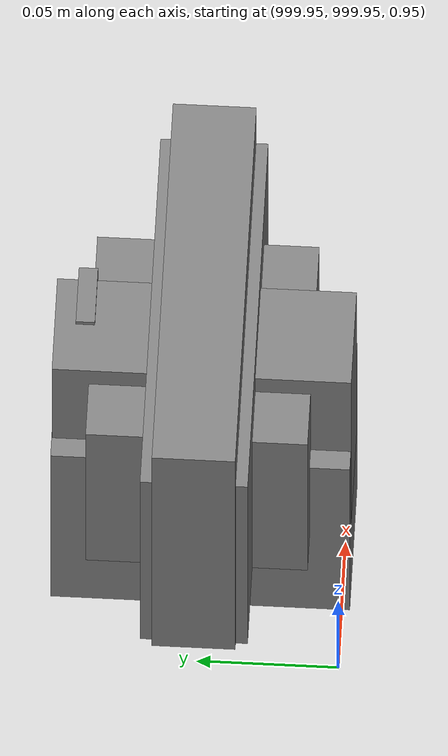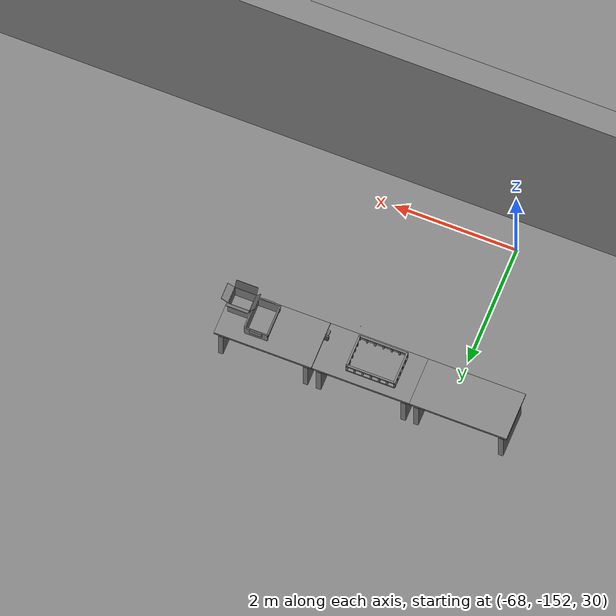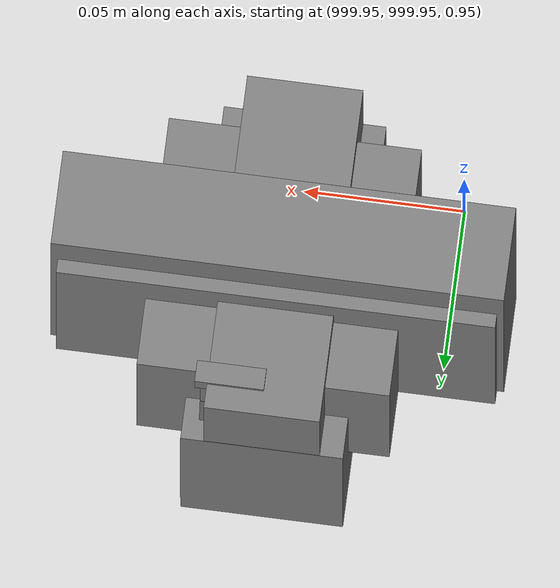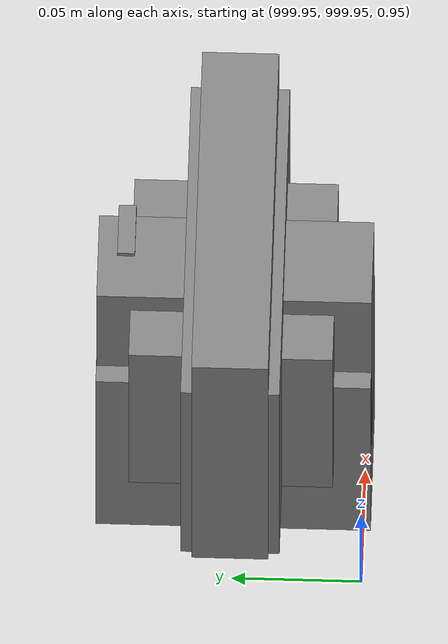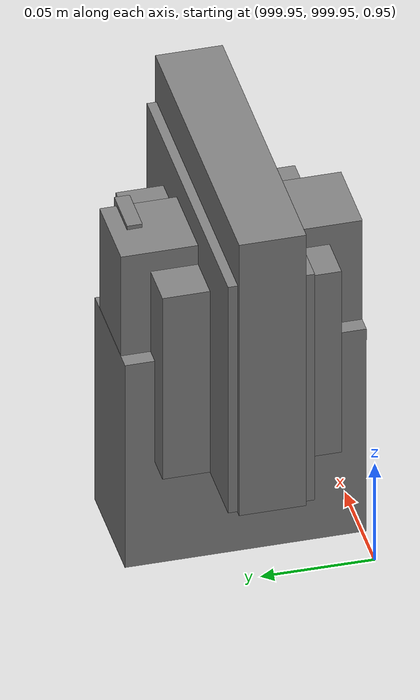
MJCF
<mujoco>
    <option gravity="0.000000000 0.000000000 -9.810000420" timestep="0.0049999999" integrator="implicitfast" density="1.225" viscosity="1.8000001e-05" noslip_iterations="10" iterations="100" sdf_iterations="50">
        <flag multiccd="disable"/>
    </option>
    <size memory="1000M"/>
    <compiler coordinate="local"/>
    <worldbody>
        <light cutoff="30" pos="0 1 1" dir="0 -1 -2"/>
        <light cutoff="30" pos="0 -1 1" dir="0 1 -2"/>
        <body pos="-64.866622925 -149.383972168 30.183746338" euler="89.999984741 89.999946594 0.000000000" name="openloong_gripper_2f85_fix_base_usda_bluebox_01">
            <geom contype="1" conaffinity="1" density="1000" type="box" material="" rgba="0.500000000 0.500000000 0.500000000 1.000000000" solimp="0.899999976 0.949999988 0.001000000" friction="1.000000000 0.005000000 0.000100000" solref="0.020000000 1.000000000" margin="0" condim="3" group="0" pos="0.276580811 0.187225342 0.000068665" quat="0.707106948 0.000077471 0.707106352 0.000077486" size="0.100000001 0.057999998 0.010000000" name="openloong_gripper_2f85_fix_base_usda_geom_77F97897_E4BE_4893_84DF_82A00B42D2C0"/>
            <geom contype="1" conaffinity="1" density="1000" type="box" material="" rgba="0.500000000 0.500000000 0.500000000 1.000000000" solimp="0.899999976 0.949999988 0.001000000" friction="1.000000000 0.005000000 0.000100000" solref="0.020000000 1.000000000" margin="0" condim="3" group="0" pos="0.000000000 0.002883911 0.000000000" quat="0.999999881 0.000000000 0.000000000 0.000000000" size="0.254000008 0.003000000 0.172000006" name="openloong_gripper_2f85_fix_base_usda_geom_3D01A6A3_6F56_49E2_8972_CE6E8C1A6016"/>
            <geom contype="1" conaffinity="1" density="1000" type="box" material="" rgba="0.500000000 0.500000000 0.500000000 1.000000000" solimp="0.899999976 0.949999988 0.001000000" friction="1.000000000 0.005000000 0.000100000" solref="0.020000000 1.000000000" margin="0" condim="3" group="0" pos="0.000000000 0.124874115 0.173484802" quat="0.999796331 0.020176515 -0.000000015 0.000000030" size="0.259999990 0.119999997 0.007000000" name="openloong_gripper_2f85_fix_base_usda_geom_82FE879A_97A8_4B6A_8FAD_7B20E2F13CB9"/>
            <geom contype="1" conaffinity="1" density="1000" type="box" material="" rgba="0.500000000 0.500000000 0.500000000 1.000000000" solimp="0.899999976 0.949999988 0.001000000" friction="1.000000000 0.005000000 0.000100000" solref="0.020000000 1.000000000" margin="0" condim="3" group="0" pos="0.000000000 0.124874115 -0.173469543" quat="0.999796331 -0.020176545 -0.000000015 0.000000000" size="0.259999990 0.119999997 0.007000000" name="openloong_gripper_2f85_fix_base_usda_geom_4F2ABF73_2C0C_429C_87F5_5F687A688CB3"/>
            <geom contype="1" conaffinity="1" density="1000" type="box" material="" rgba="0.500000000 0.500000000 0.500000000 1.000000000" solimp="0.899999976 0.949999988 0.001000000" friction="1.000000000 0.005000000 0.000100000" solref="0.020000000 1.000000000" margin="0" condim="3" group="0" pos="0.000000000 0.214008331 0.188980103" quat="0.999912977 0.013176724 0.000000015 0.000000000" size="0.259999990 0.029999999 0.012500000" name="openloong_gripper_2f85_fix_base_usda_geom_5C6F56F4_2586_406E_B7D9_D1E52D9DB355"/>
            <geom contype="1" conaffinity="1" density="1000" type="box" material="" rgba="0.500000000 0.500000000 0.500000000 1.000000000" solimp="0.899999976 0.949999988 0.001000000" friction="1.000000000 0.005000000 0.000100000" solref="0.020000000 1.000000000" margin="0" condim="3" group="0" pos="-0.258361816 0.125289917 0.001876831" quat="0.702796936 -0.020792112 0.710783124 0.020769298" size="0.189999998 0.119999997 0.009000000" name="openloong_gripper_2f85_fix_base_usda_geom_610BF1AC_02D9_40CE_865B_28AB0822028E"/>
            <geom contype="1" conaffinity="1" density="1000" type="box" material="" rgba="0.500000000 0.500000000 0.500000000 1.000000000" solimp="0.899999976 0.949999988 0.001000000" friction="1.000000000 0.005000000 0.000100000" solref="0.020000000 1.000000000" margin="0" condim="3" group="0" pos="0.000000000 0.214008331 -0.188980103" quat="0.999912977 -0.013176769 0.000000030 0.000000015" size="0.259999990 0.029999999 0.012500000" name="openloong_gripper_2f85_fix_base_usda_geom_B5DADEB4_D1B8_4762_A54F_B8972A337E9D"/>
            <geom contype="1" conaffinity="1" density="1000" type="box" material="" rgba="0.500000000 0.500000000 0.500000000 1.000000000" solimp="0.899999976 0.949999988 0.001000000" friction="1.000000000 0.005000000 0.000100000" solref="0.020000000 1.000000000" margin="0" condim="3" group="0" pos="-0.276611328 0.187225342 0.000068665" quat="0.707106650 0.000077441 0.707106709 0.000077456" size="0.100000001 0.057999998 0.010000000" name="openloong_gripper_2f85_fix_base_usda_geom_654BC1F3_25A3_494B_8117_1A8FEEAC5A83"/>
            <geom contype="1" conaffinity="1" density="1000" type="box" material="" rgba="0.500000000 0.500000000 0.500000000 1.000000000" solimp="0.899999976 0.949999988 0.001000000" friction="1.000000000 0.005000000 0.000100000" solref="0.020000000 1.000000000" margin="0" condim="3" group="0" pos="0.258331299 0.125289917 0.001876831" quat="0.702851415 0.018856421 0.710823774 -0.019329369" size="0.189999998 0.119999997 0.009000000" name="openloong_gripper_2f85_fix_base_usda_geom_E87AA55B_6FD1_4EC3_878A_4FAB23BF48A1"/>
            <freejoint name="openloong_gripper_2f85_fix_base_usda_bluebox_01_joint"/>
            <site size="0.005000000 0.005000000 0.005000000" rgba="0.500000000 0.500000000 0.500000000 1.000000000" pos="0.000000000 0.000000000 0.000000000" quat="0.999961913 0.008726534 0.000000000 0.000000000" group="0" type="sphere" name="openloong_gripper_2f85_fix_base_usda_bluebox_01site"/>
        </body>
        <body pos="-64.496299744 -149.491867065 30.235729218" euler="0.000000000 0.000000000 89.999946594" name="openloong_gripper_2f85_fix_base_usda_cardboardbox_01">
            <geom contype="1" conaffinity="1" density="1000" type="box" material="" rgba="0.500000000 0.500000000 0.500000000 1.000000000" solimp="0.899999976 0.949999988 0.001000000" friction="1.000000000 0.005000000 0.000100000" solref="0.020000000 1.000000000" margin="0" condim="3" group="0" pos="-0.003166199 -0.004086494 0.005052090" quat="1.000000000 0.000000000 0.000000000 0.000000000" size="0.142499998 0.177500010 0.005000000" name="openloong_gripper_2f85_fix_base_usda_geom_AAED9F19_52EC_4ACE_A0BD_529B3B57B93E"/>
            <geom contype="1" conaffinity="1" density="1000" type="box" material="" rgba="0.500000000 0.500000000 0.500000000 1.000000000" solimp="0.899999976 0.949999988 0.001000000" friction="1.000000000 0.005000000 0.000100000" solref="0.020000000 1.000000000" margin="0" condim="3" group="0" pos="-0.003166199 0.170316696 0.150570869" quat="1.000000000 0.000000000 0.000000000 0.000000000" size="0.142499998 0.005000000 0.149999991" name="openloong_gripper_2f85_fix_base_usda_geom_BD786805_F99D_48F1_A39F_72C6B832F39D"/>
            <geom contype="1" conaffinity="1" density="1000" type="box" material="" rgba="0.500000000 0.500000000 0.500000000 1.000000000" solimp="0.899999976 0.949999988 0.001000000" friction="1.000000000 0.005000000 0.000100000" solref="0.020000000 1.000000000" margin="0" condim="3" group="0" pos="-0.147399902 -0.005307198 0.150570869" quat="1.000000000 0.000000000 0.000000000 0.000000000" size="0.005000000 0.177500010 0.149999991" name="openloong_gripper_2f85_fix_base_usda_geom_164515AB_DFE2_4A0C_8E6E_052CFB55062C"/>
            <geom contype="1" conaffinity="1" density="1000" type="box" material="" rgba="0.500000000 0.500000000 0.500000000 1.000000000" solimp="0.899999976 0.949999988 0.001000000" friction="1.000000000 0.005000000 0.000100000" solref="0.020000000 1.000000000" margin="0" condim="3" group="0" pos="0.140275955 -0.005307198 0.150570869" quat="1.000000000 0.000000000 0.000000000 0.000000000" size="0.005000000 0.177500010 0.149999991" name="openloong_gripper_2f85_fix_base_usda_geom_ED55E7A0_00E0_4184_81EC_149F0896EC29"/>
            <geom contype="1" conaffinity="1" density="1000" type="box" material="" rgba="0.500000000 0.500000000 0.500000000 1.000000000" solimp="0.899999976 0.949999988 0.001000000" friction="1.000000000 0.005000000 0.000100000" solref="0.020000000 1.000000000" margin="0" condim="3" group="0" pos="-0.003166199 -0.181550980 0.150570869" quat="1.000000000 0.000000000 0.000000000 0.000000000" size="0.142499998 0.005000000 0.149999991" name="openloong_gripper_2f85_fix_base_usda_geom_188FDBA9_ABB8_4192_9060_1858EC86DDA8"/>
            <freejoint name="openloong_gripper_2f85_fix_base_usda_cardboardbox_01_joint"/>
            <site size="0.005000000 0.005000000 0.005000000" rgba="0.500000000 0.500000000 0.500000000 1.000000000" pos="0.000000000 0.000000000 0.000000000" quat="0.999961913 0.008726535 0.000000000 0.000000000" group="0" type="sphere" name="openloong_gripper_2f85_fix_base_usda_site_E403B3B3_8095_4E7E_AD11_E733E5C8606F"/>
            <body pos="0.139160156 -0.004048347 0.301930904" euler="-179.999954224 49.383502960 179.999954224" name="openloong_gripper_2f85_fix_base_usda_A1_006">
                <geom contype="1" conaffinity="1" density="1000" type="box" material="" rgba="0.500000000 0.500000000 0.500000000 1.000000000" solimp="0.899999976 0.949999988 0.001000000" friction="1.000000000 0.005000000 0.000100000" solref="0.020000000 1.000000000" margin="0" condim="3" group="0" pos="-0.071587563 0.000009537 0.001745224" quat="0.999999881 0.000000000 0.000000000 0.000000000" size="0.071249999 0.179999992 0.002500000" name="openloong_gripper_2f85_fix_base_usda_geom_EE9B1BA0_6D67_4976_825A_22E9680929F2"/>
                <joint armature="0" stiffness="0.07" damping="0.0099999998" axis="0.000000 1.000000 0.000000" type="hinge" name="openloong_gripper_2f85_fix_base_usda_A1_006"/>
            </body>
            <body pos="-0.145902634 -0.004086494 0.301938057" euler="-180.000000000 -60.000011444 -180.000000000" name="openloong_gripper_2f85_fix_base_usda_A2_006">
                <geom contype="1" conaffinity="1" density="1000" type="box" material="" rgba="0.500000000 0.500000000 0.500000000 1.000000000" solimp="0.899999976 0.949999988 0.001000000" friction="1.000000000 0.005000000 0.000100000" solref="0.020000000 1.000000000" margin="0" condim="3" group="0" pos="0.071268082 0.000009537 0.002717972" quat="0.000002921 0.000000000 -0.000000030 0.999999881" size="0.071249999 0.179999992 0.002500000" name="openloong_gripper_2f85_fix_base_usda_geom_25817274_E996_41B9_8E29_4FB5B82E8024"/>
                <joint armature="0" stiffness="0.07" damping="0.0099999998" axis="0.000000 1.000000 0.000000" type="hinge" name="openloong_gripper_2f85_fix_base_usda_A2_006"/>
            </body>
            <body pos="-0.003385544 0.175991058 0.301930904" euler="-125.858116150 -0.000004561 0.000002331" name="openloong_gripper_2f85_fix_base_usda_B2_006">
                <geom contype="1" conaffinity="1" density="1000" type="box" material="" rgba="0.500000000 0.500000000 0.500000000 1.000000000" solimp="0.899999976 0.949999988 0.001000000" friction="1.000000000 0.005000000 0.000100000" solref="0.020000000 1.000000000" margin="0" condim="3" group="0" pos="0.000009537 -0.070939064 -0.002470016" quat="0.999614120 0.027776197 -0.000000015 0.000000030" size="0.137500003 0.064999998 0.005000000" name="openloong_gripper_2f85_fix_base_usda_geom_7015A3BF_735C_455B_A3BC_4AD683FD94E0"/>
                <joint armature="0" stiffness="0.07" damping="0.0099999998" axis="1.000000 0.000000 0.000000" type="hinge" name="openloong_gripper_2f85_fix_base_usda_B2_006"/>
            </body>
            <body pos="-0.003385544 -0.184140205 0.301938057" euler="147.805557251 0.000000000 0.000000000" name="openloong_gripper_2f85_fix_base_usda_B1_006">
                <geom contype="1" conaffinity="1" density="1000" type="box" material="" rgba="0.500000000 0.500000000 0.500000000 1.000000000" solimp="0.899999976 0.949999988 0.001000000" friction="1.000000000 0.005000000 0.000100000" solref="0.020000000 1.000000000" margin="0" condim="3" group="0" pos="-0.000028610 0.070202351 -0.002703667" quat="0.999614179 -0.027776167 0.000000000 0.000000000" size="0.137500003 0.064999998 0.005000000" name="openloong_gripper_2f85_fix_base_usda_geom_11CFBAF6_9E61_4903_8260_9788E07372C1"/>
                <joint armature="0" stiffness="0.07" damping="0.0099999998" axis="1.000000 0.000000 0.000000" type="hinge" name="openloong_gripper_2f85_fix_base_usda_B1_006"/>
            </body>
        </body>
        <body pos="-65.882858276 -149.481979370 30.229999542" euler="-64.487716675 0.000000000 0.000000000" name="openloong_gripper_2f85_fix_base_usda_Barcode">
            <geom contype="1" conaffinity="1" density="1000" type="box" material="" rgba="0.500000000 0.500000000 0.500000000 1.000000000" solimp="0.899999976 0.949999988 0.001000000" friction="1.000000000 0.005000000 0.000100000" solref="0.020000000 1.000000000" margin="0" condim="3" group="0" pos="0.000000000 0.013038635 0.001419067" quat="0.000000000 0.000000000 0.000000000 1.000000119" size="0.034000002 0.010000000 0.017999999" name="openloong_gripper_2f85_fix_base_usda_geom_638769FF_FC71_4B34_89B3_A7DBF27AA68D"/>
            <geom contype="1" conaffinity="1" density="1000" type="box" material="" rgba="0.500000000 0.500000000 0.500000000 1.000000000" solimp="0.899999976 0.949999988 0.001000000" friction="1.000000000 0.005000000 0.000100000" solref="0.020000000 1.000000000" margin="0" condim="3" group="0" pos="0.000000000 -0.035301208 -0.007095337" quat="0.000000000 0.000000000 -0.043619365 0.999048233" size="0.028999999 0.010000000 0.020000000" name="openloong_gripper_2f85_fix_base_usda_geom_0191FADB_8E15_49D0_A1FC_CF019DC21CAB"/>
            <geom contype="1" conaffinity="1" density="1000" type="box" material="" rgba="0.500000000 0.500000000 0.500000000 1.000000000" solimp="0.899999976 0.949999988 0.001000000" friction="1.000000000 0.005000000 0.000100000" solref="0.020000000 1.000000000" margin="0" condim="3" group="0" pos="0.000000000 -0.043411255 -0.011749268" quat="0.922262907 0.386563420 0.000000000 0.000000000" size="0.026000001 0.010000000 0.020000000" name="openloong_gripper_2f85_fix_base_usda_geom_5203DB7B_BF8E_42A4_9A7E_8E3FF6712F24"/>
            <geom contype="1" conaffinity="1" density="1000" type="box" material="" rgba="0.500000000 0.500000000 0.500000000 1.000000000" solimp="0.899999976 0.949999988 0.001000000" friction="1.000000000 0.005000000 0.000100000" solref="0.020000000 1.000000000" margin="0" condim="3" group="0" pos="0.000000000 -0.016967773 -0.031860352" quat="0.000000000 0.000000000 0.000000000 1.000000119" size="0.008000000 0.010000000 0.013000000" name="openloong_gripper_2f85_fix_base_usda_geom_DBC0D5BA_7F4B_452A_8B1F_4836E692B5D2"/>
            <geom contype="1" conaffinity="1" density="1000" type="box" material="" rgba="0.500000000 0.500000000 0.500000000 1.000000000" solimp="0.899999976 0.949999988 0.001000000" friction="1.000000000 0.005000000 0.000100000" solref="0.020000000 1.000000000" margin="0" condim="3" group="0" pos="0.000000000 -0.001869202 0.000312805" quat="0.953716993 0.300705761 0.000000000 0.000000000" size="0.032000002 0.010000000 0.018999999" name="openloong_gripper_2f85_fix_base_usda_geom_22F162A9_5583_42F6_B82C_77471C257E6F"/>
            <geom contype="1" conaffinity="1" density="1000" type="box" material="" rgba="0.500000000 0.500000000 0.500000000 1.000000000" solimp="0.899999976 0.949999988 0.001000000" friction="1.000000000 0.005000000 0.000100000" solref="0.020000000 1.000000000" margin="0" condim="3" group="0" pos="0.000000000 -0.019531250 -0.003173828" quat="0.953716993 0.300705761 0.000000000 0.000000000" size="0.030999999 0.010000000 0.020000000" name="openloong_gripper_2f85_fix_base_usda_geom_3E59D9B5_8010_4FD4_B0A2_40F386528BD7"/>
            <geom contype="1" conaffinity="1" density="1000" type="box" material="" rgba="0.500000000 0.500000000 0.500000000 1.000000000" solimp="0.899999976 0.949999988 0.001000000" friction="1.000000000 0.005000000 0.000100000" solref="0.020000000 1.000000000" margin="0" condim="3" group="0" pos="0.000000000 -0.035301208 -0.007095337" quat="0.953716993 0.300705761 0.000000000 0.000000000" size="0.028999999 0.010000000 0.020000000" name="openloong_gripper_2f85_fix_base_usda_geom_B6452ED4_4A28_401D_BC66_212DDEE8F750"/>
            <geom contype="1" conaffinity="1" density="1000" type="box" material="" rgba="0.500000000 0.500000000 0.500000000 1.000000000" solimp="0.899999976 0.949999988 0.001000000" friction="1.000000000 0.005000000 0.000100000" solref="0.020000000 1.000000000" margin="0" condim="3" group="0" pos="0.000000000 -0.042617798 -0.071121216" quat="0.000000000 0.000000000 0.000000000 1.000000119" size="0.013000000 0.021000000 0.059999999" name="openloong_gripper_2f85_fix_base_usda_geom_D8B9E205_F8E8_4E87_B3E0_AAD9349564FB"/>
            <freejoint name="openloong_gripper_2f85_fix_base_usda_Barcode_joint"/>
            <site size="0.005000000 0.005000000 0.005000000" rgba="0.500000000 0.500000000 0.500000000 1.000000000" pos="0.000000000 0.000000000 0.000000000" quat="1.000000000 0.000000000 0.000000000 0.000000000" group="0" type="sphere" name="openloong_gripper_2f85_fix_base_usda_Barcode_site"/>
        </body>
        <body pos="-66.745018005 -149.392349243 30.184000015" euler="0.000000000 0.000000000 89.999946594" name="[22331891527752]_Basket_01">
            <geom contype="1" conaffinity="1" density="1000" type="box" material="" rgba="0.500000000 0.500000000 0.500000000 1.000000000" solimp="0.899999976 0.949999988 0.001000000" friction="1.000000000 0.005000000 0.000100000" solref="0.020000000 1.000000000" margin="0" condim="3" group="0" pos="-0.052425385 0.389207840 0.089787483" quat="0.707107008 0.000000000 0.000000000 0.707106411" size="0.014249999 0.014249999 0.059999999" name="[22331891527752]_geom_1C9A57FD_5186_4EBC_A866_E83FCA69D2AE"/>
            <geom contype="1" conaffinity="1" density="1000" type="box" material="" rgba="0.500000000 0.500000000 0.500000000 1.000000000" solimp="0.899999976 0.949999988 0.001000000" friction="1.000000000 0.005000000 0.000100000" solref="0.020000000 1.000000000" margin="0" condim="3" group="0" pos="0.264015198 -0.133043289 0.089787483" quat="0.707107008 0.000000000 0.000000000 0.707106411" size="0.014249999 0.014249999 0.059999999" name="[22331891527752]_geom_8E1F1D59_56A4_492F_B04D_57F2BA3E33D4"/>
            <geom contype="1" conaffinity="1" density="1000" type="box" material="" rgba="0.500000000 0.500000000 0.500000000 1.000000000" solimp="0.899999976 0.949999988 0.001000000" friction="1.000000000 0.005000000 0.000100000" solref="0.020000000 1.000000000" margin="0" condim="3" group="0" pos="-0.264015198 -0.265548706 0.089793205" quat="0.707107008 0.000000000 0.000000000 0.707106411" size="0.014249999 0.014249999 0.059999999" name="[22331891527752]_geom_E9D41D99_7FDB_4570_B421_7FDFABBBE557"/>
            <geom contype="1" conaffinity="1" density="1000" type="box" material="" rgba="0.500000000 0.500000000 0.500000000 1.000000000" solimp="0.899999976 0.949999988 0.001000000" friction="1.000000000 0.005000000 0.000100000" solref="0.020000000 1.000000000" margin="0" condim="3" group="0" pos="-0.160263062 -0.389322281 0.089793205" quat="0.707107008 0.000000000 0.000000000 0.707106411" size="0.014249999 0.014249999 0.059999999" name="[22331891527752]_geom_9B4BC987_1883_4D13_81C2_80D0EB5B7B42"/>
            <geom contype="1" conaffinity="1" density="1000" type="box" material="" rgba="0.500000000 0.500000000 0.500000000 1.000000000" solimp="0.899999976 0.949999988 0.001000000" friction="1.000000000 0.005000000 0.000100000" solref="0.020000000 1.000000000" margin="0" condim="3" group="0" pos="0.162265778 -0.389322281 0.089787483" quat="0.707107008 0.000000000 0.000000000 0.707106411" size="0.014249999 0.014249999 0.059999999" name="[22331891527752]_geom_C32750DB_F7E8_4E13_8707_E9540E20D14E"/>
            <geom contype="1" conaffinity="1" density="1000" type="box" material="" rgba="0.500000000 0.500000000 0.500000000 1.000000000" solimp="0.899999976 0.949999988 0.001000000" friction="1.000000000 0.005000000 0.000100000" solref="0.020000000 1.000000000" margin="0" condim="3" group="0" pos="0.264015198 0.389207840 0.089787483" quat="0.707107008 0.000000000 0.000000000 0.707106411" size="0.014249999 0.014249999 0.059999999" name="[22331891527752]_geom_DF3D1415_EFAE_4F80_95C8_FD76007D50DD"/>
            <geom contype="1" conaffinity="1" density="1000" type="box" material="" rgba="0.500000000 0.500000000 0.500000000 1.000000000" solimp="0.899999976 0.949999988 0.001000000" friction="1.000000000 0.005000000 0.000100000" solref="0.020000000 1.000000000" margin="0" condim="3" group="0" pos="-0.264015198 -0.133043289 0.089793205" quat="0.707107008 0.000000000 0.000000000 0.707106411" size="0.014249999 0.014249999 0.059999999" name="[22331891527752]_geom_C1DC5D17_D0FF_4863_8CF9_627EE1498067"/>
            <geom contype="1" conaffinity="1" density="1000" type="box" material="" rgba="0.500000000 0.500000000 0.500000000 1.000000000" solimp="0.899999976 0.949999988 0.001000000" friction="1.000000000 0.005000000 0.000100000" solref="0.020000000 1.000000000" margin="0" condim="3" group="0" pos="-0.264026642 0.269256592 0.089793205" quat="0.707107008 0.000000000 0.000000000 0.707106411" size="0.014249999 0.014249999 0.059999999" name="[22331891527752]_geom_EB4FC47B_BE0C_4D85_B597_360A68EC6148"/>
            <geom contype="1" conaffinity="1" density="1000" type="box" material="" rgba="0.500000000 0.500000000 0.500000000 1.000000000" solimp="0.899999976 0.949999988 0.001000000" friction="1.000000000 0.005000000 0.000100000" solref="0.020000000 1.000000000" margin="0" condim="3" group="0" pos="0.054462433 0.389207840 0.089787483" quat="0.707107008 0.000000000 0.000000000 0.707106411" size="0.014249999 0.014249999 0.059999999" name="[22331891527752]_geom_B77E756C_877F_4EA6_A4F4_4602C7E06D11"/>
            <geom contype="1" conaffinity="1" density="1000" type="box" material="" rgba="0.500000000 0.500000000 0.500000000 1.000000000" solimp="0.899999976 0.949999988 0.001000000" friction="1.000000000 0.005000000 0.000100000" solref="0.020000000 1.000000000" margin="0" condim="3" group="0" pos="0.054462433 -0.389322281 0.089787483" quat="0.707107008 0.000000000 0.000000000 0.707106411" size="0.014249999 0.014249999 0.059999999" name="[22331891527752]_geom_A6BF6153_751B_4F26_BFCB_BFAE6296E51F"/>
            <geom contype="1" conaffinity="1" density="1000" type="box" material="" rgba="0.500000000 0.500000000 0.500000000 1.000000000" solimp="0.899999976 0.949999988 0.001000000" friction="1.000000000 0.005000000 0.000100000" solref="0.020000000 1.000000000" margin="0" condim="3" group="0" pos="0.264015198 0.269256592 0.089793205" quat="0.707107008 0.000000000 0.000000000 0.707106411" size="0.014249999 0.014249999 0.059999999" name="[22331891527752]_geom_48D65F5E_ED62_4714_93A7_B9119ED5FBB1"/>
            <geom contype="1" conaffinity="1" density="1000" type="box" material="" rgba="0.500000000 0.500000000 0.500000000 1.000000000" solimp="0.899999976 0.949999988 0.001000000" friction="1.000000000 0.005000000 0.000100000" solref="0.020000000 1.000000000" margin="0" condim="3" group="0" pos="0.264015198 -0.389322281 0.089787483" quat="0.707107008 0.000000000 0.000000000 0.707106411" size="0.014249999 0.014249999 0.059999999" name="[22331891527752]_geom_7E9A7560_BCB0_4C4E_9FA2_59D637DB159A"/>
            <geom contype="1" conaffinity="1" density="1000" type="box" material="" rgba="0.500000000 0.500000000 0.500000000 1.000000000" solimp="0.899999976 0.949999988 0.001000000" friction="1.000000000 0.005000000 0.000100000" solref="0.020000000 1.000000000" margin="0" condim="3" group="0" pos="0.000000000 0.000000000 0.015998840" quat="0.707107008 0.000000000 0.000000000 0.707106411" size="0.403499991 0.279000014 0.015750000" name="[22331891527752]_geom_B2E3EE19_D293_4B08_8253_71473787E73C"/>
            <geom contype="1" conaffinity="1" density="1000" type="box" material="" rgba="0.500000000 0.500000000 0.500000000 1.000000000" solimp="0.899999976 0.949999988 0.001000000" friction="1.000000000 0.005000000 0.000100000" solref="0.020000000 1.000000000" margin="0" condim="3" group="0" pos="0.000000000 -0.389476776 0.163619041" quat="0.707107008 0.000000000 0.000000000 0.707106411" size="0.015000000 0.277500004 0.015750000" name="[22331891527752]_geom_E4DFC5A8_7697_48CD_9AD3_084CCEC5279D"/>
            <geom contype="1" conaffinity="1" density="1000" type="box" material="" rgba="0.500000000 0.500000000 0.500000000 1.000000000" solimp="0.899999976 0.949999988 0.001000000" friction="1.000000000 0.005000000 0.000100000" solref="0.020000000 1.000000000" margin="0" condim="3" group="0" pos="0.162265778 0.389207840 0.089787483" quat="0.707107008 0.000000000 0.000000000 0.707106411" size="0.014249999 0.014249999 0.059999999" name="[22331891527752]_geom_DD104512_D81B_43C0_BB1A_B673E49CEF94"/>
            <geom contype="1" conaffinity="1" density="1000" type="box" material="" rgba="0.500000000 0.500000000 0.500000000 1.000000000" solimp="0.899999976 0.949999988 0.001000000" friction="1.000000000 0.005000000 0.000100000" solref="0.020000000 1.000000000" margin="0" condim="3" group="0" pos="0.000000000 0.389471054 0.163619041" quat="0.707107008 0.000000000 0.000000000 0.707106411" size="0.015000000 0.277500004 0.015750000" name="[22331891527752]_geom_341CFD76_576B_4A35_B410_835E75D8C6DC"/>
            <geom contype="1" conaffinity="1" density="1000" type="box" material="" rgba="0.500000000 0.500000000 0.500000000 1.000000000" solimp="0.899999976 0.949999988 0.001000000" friction="1.000000000 0.005000000 0.000100000" solref="0.020000000 1.000000000" margin="0" condim="3" group="0" pos="-0.263511658 0.000000000 0.163619041" quat="0.707107008 0.000000000 0.000000000 0.707106411" size="0.403499991 0.015000000 0.015750000" name="[22331891527752]_geom_048723E6_7A7C_4725_9E7D_D2940FADDB3D"/>
            <geom contype="1" conaffinity="1" density="1000" type="box" material="" rgba="0.500000000 0.500000000 0.500000000 1.000000000" solimp="0.899999976 0.949999988 0.001000000" friction="1.000000000 0.005000000 0.000100000" solref="0.020000000 1.000000000" margin="0" condim="3" group="0" pos="-0.264015198 0.141334534 0.089793205" quat="0.707107008 0.000000000 0.000000000 0.707106411" size="0.014249999 0.014249999 0.059999999" name="[22331891527752]_geom_F6A10A99_277D_4904_A8FA_067B6C6F44FC"/>
            <geom contype="1" conaffinity="1" density="1000" type="box" material="" rgba="0.500000000 0.500000000 0.500000000 1.000000000" solimp="0.899999976 0.949999988 0.001000000" friction="1.000000000 0.005000000 0.000100000" solref="0.020000000 1.000000000" margin="0" condim="3" group="0" pos="0.264015198 -0.265548706 0.089787483" quat="0.707107008 0.000000000 0.000000000 0.707106411" size="0.014249999 0.014249999 0.059999999" name="[22331891527752]_geom_B5EED248_F3A4_4AC7_9908_CDDD8B5DC44F"/>
            <geom contype="1" conaffinity="1" density="1000" type="box" material="" rgba="0.500000000 0.500000000 0.500000000 1.000000000" solimp="0.899999976 0.949999988 0.001000000" friction="1.000000000 0.005000000 0.000100000" solref="0.020000000 1.000000000" margin="0" condim="3" group="0" pos="-0.160263062 0.389207840 0.089787483" quat="0.707107008 0.000000000 0.000000000 0.707106411" size="0.014249999 0.014249999 0.059999999" name="[22331891527752]_geom_377313AE_9170_407D_BEF1_58AAEC4CE068"/>
            <geom contype="1" conaffinity="1" density="1000" type="box" material="" rgba="0.500000000 0.500000000 0.500000000 1.000000000" solimp="0.899999976 0.949999988 0.001000000" friction="1.000000000 0.005000000 0.000100000" solref="0.020000000 1.000000000" margin="0" condim="3" group="0" pos="-0.052425385 -0.389322281 0.089787483" quat="0.707107008 0.000000000 0.000000000 0.707106411" size="0.014249999 0.014249999 0.059999999" name="[22331891527752]_geom_D38B6FC6_B8D0_479F_8375_C79304854923"/>
            <geom contype="1" conaffinity="1" density="1000" type="box" material="" rgba="0.500000000 0.500000000 0.500000000 1.000000000" solimp="0.899999976 0.949999988 0.001000000" friction="1.000000000 0.005000000 0.000100000" solref="0.020000000 1.000000000" margin="0" condim="3" group="0" pos="-0.264026642 -0.389322281 0.089793205" quat="0.707107008 0.000000000 0.000000000 0.707106411" size="0.014249999 0.014249999 0.059999999" name="[22331891527752]_geom_F2FE1E91_B5A3_4C82_BA96_5E1DDCB57D49"/>
            <geom contype="1" conaffinity="1" density="1000" type="box" material="" rgba="0.500000000 0.500000000 0.500000000 1.000000000" solimp="0.899999976 0.949999988 0.001000000" friction="1.000000000 0.005000000 0.000100000" solref="0.020000000 1.000000000" margin="0" condim="3" group="0" pos="0.264015198 0.141334534 0.089787483" quat="0.707107008 0.000000000 0.000000000 0.707106411" size="0.014249999 0.014249999 0.059999999" name="[22331891527752]_geom_B50731B8_3BD2_4DCD_923F_A4A806F5AE22"/>
            <geom contype="1" conaffinity="1" density="1000" type="box" material="" rgba="0.500000000 0.500000000 0.500000000 1.000000000" solimp="0.899999976 0.949999988 0.001000000" friction="1.000000000 0.005000000 0.000100000" solref="0.020000000 1.000000000" margin="0" condim="3" group="0" pos="-0.264015198 0.389207840 0.089793205" quat="0.707107008 0.000000000 0.000000000 0.707106411" size="0.014249999 0.014249999 0.059999999" name="[22331891527752]_geom_9539FD0A_302D_45F9_A56D_7FE15110AEB2"/>
            <geom contype="1" conaffinity="1" density="1000" type="box" material="" rgba="0.500000000 0.500000000 0.500000000 1.000000000" solimp="0.899999976 0.949999988 0.001000000" friction="1.000000000 0.005000000 0.000100000" solref="0.020000000 1.000000000" margin="0" condim="3" group="0" pos="0.264015198 0.004480362 0.089787483" quat="0.707107008 0.000000000 0.000000000 0.707106411" size="0.014249999 0.014249999 0.059999999" name="[22331891527752]_geom_5B9D82AD_8BDE_455A_B71F_6A5403B0A1CF"/>
            <geom contype="1" conaffinity="1" density="1000" type="box" material="" rgba="0.500000000 0.500000000 0.500000000 1.000000000" solimp="0.899999976 0.949999988 0.001000000" friction="1.000000000 0.005000000 0.000100000" solref="0.020000000 1.000000000" margin="0" condim="3" group="0" pos="0.263694763 -0.000011444 0.163619041" quat="0.707107008 0.000000000 0.000000000 0.707106411" size="0.403499991 0.015000000 0.015750000" name="[22331891527752]_geom_A60B5927_F74A_419B_B3F0_3782488B3229"/>
            <geom contype="1" conaffinity="1" density="1000" type="box" material="" rgba="0.500000000 0.500000000 0.500000000 1.000000000" solimp="0.899999976 0.949999988 0.001000000" friction="1.000000000 0.005000000 0.000100000" solref="0.020000000 1.000000000" margin="0" condim="3" group="0" pos="-0.264015198 0.004480362 0.089793205" quat="0.707107008 0.000000000 0.000000000 0.707106411" size="0.014249999 0.014249999 0.059999999" name="[22331891527752]_geom_B16EDFF9_A165_480E_B299_EC0BBC5DFBB4"/>
            <freejoint name="[22331891527752]_joint_1F4EDA52_A408_4A27_BEEF_2769BB3F8FB1"/>
        </body>
        <body pos="0.000000000 0.000000000 0.000000000" euler="0.000000000 0.000000000 0.000000000" name="Static Objects_Static Objects">
            <geom contype="1" conaffinity="1" density="1000" type="box" material="" rgba="0.500000000 0.500000000 0.500000000 1.000000000" solimp="0.899999976 0.949999988 0.001000000" friction="1.000000000 0.005000000 0.000100000" solref="0.020000000 1.000000000" margin="0" condim="3" group="0" pos="-67.544113159 -149.365814209 29.727830887" quat="0.500000417 0.499999970 0.499999553 0.499999970" size="0.381000012 0.319999993 0.041000001" name="Static Objects_geom_4267055F_8C54_4978_AFC3_5A1AA8BC6309"/>
            <geom contype="1" conaffinity="1" density="1000" type="box" material="" rgba="0.500000000 0.500000000 0.500000000 1.000000000" solimp="0.899999976 0.949999988 0.001000000" friction="1.000000000 0.005000000 0.000100000" solref="0.020000000 1.000000000" margin="0" condim="3" group="0" pos="-68.239501953 -149.365814209 30.086868286" quat="0.500000417 0.499999970 0.499999553 0.499999970" size="0.370999992 0.039500002 0.745000005" name="Static Objects_geom_9C3765D6_B08F_4106_82DF_EEE142A4E005"/>
            <geom contype="1" conaffinity="1" density="1000" type="box" material="" rgba="0.500000000 0.500000000 0.500000000 1.000000000" solimp="0.899999976 0.949999988 0.001000000" friction="1.000000000 0.005000000 0.000100000" solref="0.020000000 1.000000000" margin="0" condim="3" group="0" pos="-68.239501953 -149.365814209 30.147235870" quat="0.500000417 0.499999970 0.499999553 0.499999970" size="0.400000006 0.022000000 0.800000012" name="Static Objects_geom_00EFF775_4521_4DEC_A9E0_63A7B3757AEE"/>
            <geom contype="1" conaffinity="1" density="1000" type="box" material="" rgba="0.500000000 0.500000000 0.500000000 1.000000000" solimp="0.899999976 0.949999988 0.001000000" friction="1.000000000 0.005000000 0.000100000" solref="0.020000000 1.000000000" margin="0" condim="3" group="0" pos="-68.934890747 -149.365814209 29.727830887" quat="0.500000417 0.499999970 0.499999553 0.499999970" size="0.381000012 0.319999993 0.041000001" name="Static Objects_geom_D6F8F0B7_4461_40D4_A04B_E13CF73E9317"/>
            <geom contype="1" conaffinity="1" density="1000" type="box" material="" rgba="0.500000000 0.500000000 0.500000000 1.000000000" solimp="0.899999976 0.949999988 0.001000000" friction="1.000000000 0.005000000 0.000100000" solref="0.020000000 1.000000000" margin="0" condim="3" group="0" pos="-68.239501953 -149.365814209 29.561563492" quat="0.500000417 0.499999970 0.499999553 0.499999970" size="0.020000000 0.022000000 0.660000026" name="Static Objects_geom_A544A7D3_AE2F_43EA_9E97_6982F193D0AF"/>
            <geom contype="1" conaffinity="1" density="1000" type="box" material="" rgba="0.500000000 0.500000000 0.500000000 1.000000000" solimp="0.899999976 0.949999988 0.001000000" friction="1.000000000 0.005000000 0.000100000" solref="0.020000000 1.000000000" margin="0" condim="3" group="0" pos="-65.945671082 -149.365814209 29.727830887" quat="0.500000417 0.499999970 0.499999553 0.499999970" size="0.381000012 0.319999993 0.041000001" name="Static Objects_geom_55BC22BA_377A_42F7_95B8_6BB5FDDFBBA1"/>
            <geom contype="1" conaffinity="1" density="1000" type="box" material="" rgba="0.500000000 0.500000000 0.500000000 1.000000000" solimp="0.899999976 0.949999988 0.001000000" friction="1.000000000 0.005000000 0.000100000" solref="0.020000000 1.000000000" margin="0" condim="3" group="0" pos="-66.641059875 -149.365814209 30.086868286" quat="0.500000417 0.499999970 0.499999553 0.499999970" size="0.370999992 0.039500002 0.745000005" name="Static Objects_geom_CEB1FA77_E109_4D31_869B_8BC64D395B6B"/>
            <geom contype="1" conaffinity="1" density="1000" type="box" material="" rgba="0.500000000 0.500000000 0.500000000 1.000000000" solimp="0.899999976 0.949999988 0.001000000" friction="1.000000000 0.005000000 0.000100000" solref="0.020000000 1.000000000" margin="0" condim="3" group="0" pos="-66.641059875 -149.365814209 30.147235870" quat="0.500000417 0.499999970 0.499999553 0.499999970" size="0.400000006 0.022000000 0.800000012" name="Static Objects_geom_D180A674_CB27_47FA_9BAA_C1CAB2A5F2F9"/>
            <geom contype="1" conaffinity="1" density="1000" type="box" material="" rgba="0.500000000 0.500000000 0.500000000 1.000000000" solimp="0.899999976 0.949999988 0.001000000" friction="1.000000000 0.005000000 0.000100000" solref="0.020000000 1.000000000" margin="0" condim="3" group="0" pos="-67.336448669 -149.365814209 29.727830887" quat="0.500000417 0.499999970 0.499999553 0.499999970" size="0.381000012 0.319999993 0.041000001" name="Static Objects_geom_609A2007_031D_43A7_916C_B6B19C6C05E7"/>
            <geom contype="1" conaffinity="1" density="1000" type="box" material="" rgba="0.500000000 0.500000000 0.500000000 1.000000000" solimp="0.899999976 0.949999988 0.001000000" friction="1.000000000 0.005000000 0.000100000" solref="0.020000000 1.000000000" margin="0" condim="3" group="0" pos="-66.641059875 -149.365814209 29.561563492" quat="0.500000417 0.499999970 0.499999553 0.499999970" size="0.020000000 0.022000000 0.660000026" name="Static Objects_geom_0DE7D064_506F_4D3C_B81B_B803AA7CAE66"/>
            <geom contype="1" conaffinity="1" density="1000" type="box" material="" rgba="0.500000000 0.500000000 0.500000000 1.000000000" solimp="0.899999976 0.949999988 0.001000000" friction="1.000000000 0.005000000 0.000100000" solref="0.020000000 1.000000000" margin="0" condim="3" group="0" pos="-64.338577271 -149.365814209 29.727830887" quat="0.500000417 0.499999970 0.499999553 0.499999970" size="0.381000012 0.319999993 0.041000001" name="Static Objects_geom_6DEFF9FA_9569_4616_B8A8_4979658A3034"/>
            <geom contype="1" conaffinity="1" density="1000" type="box" material="" rgba="0.500000000 0.500000000 0.500000000 1.000000000" solimp="0.899999976 0.949999988 0.001000000" friction="1.000000000 0.005000000 0.000100000" solref="0.020000000 1.000000000" margin="0" condim="3" group="0" pos="-65.033966064 -149.365814209 30.086868286" quat="0.500000417 0.499999970 0.499999553 0.499999970" size="0.370999992 0.039500002 0.745000005" name="Static Objects_geom_085C0D21_FA30_4F95_BA27_1997C9F4FCC1"/>
            <geom contype="1" conaffinity="1" density="1000" type="box" material="" rgba="0.500000000 0.500000000 0.500000000 1.000000000" solimp="0.899999976 0.949999988 0.001000000" friction="1.000000000 0.005000000 0.000100000" solref="0.020000000 1.000000000" margin="0" condim="3" group="0" pos="-65.033966064 -149.365814209 30.147235870" quat="0.500000417 0.499999970 0.499999553 0.499999970" size="0.400000006 0.022000000 0.800000012" name="Static Objects_geom_0E6DF55E_4B23_4BE7_A164_651F32A85E06"/>
            <geom contype="1" conaffinity="1" density="1000" type="box" material="" rgba="0.500000000 0.500000000 0.500000000 1.000000000" solimp="0.899999976 0.949999988 0.001000000" friction="1.000000000 0.005000000 0.000100000" solref="0.020000000 1.000000000" margin="0" condim="3" group="0" pos="-65.729354858 -149.365814209 29.727830887" quat="0.500000417 0.499999970 0.499999553 0.499999970" size="0.381000012 0.319999993 0.041000001" name="Static Objects_geom_3D9C0E6F_AF07_4566_A089_BFB51143C2C8"/>
            <geom contype="1" conaffinity="1" density="1000" type="box" material="" rgba="0.500000000 0.500000000 0.500000000 1.000000000" solimp="0.899999976 0.949999988 0.001000000" friction="1.000000000 0.005000000 0.000100000" solref="0.020000000 1.000000000" margin="0" condim="3" group="0" pos="-65.033966064 -149.365814209 29.561563492" quat="0.500000417 0.499999970 0.499999553 0.499999970" size="0.020000000 0.022000000 0.660000026" name="Static Objects_geom_E924F3AD_ADD0_44ED_8BF2_9107BBA2CCAE"/>
            <geom contype="1" conaffinity="1" density="1000" type="box" material="" rgba="0.500000000 0.500000000 0.500000000 1.000000000" solimp="0.899999976 0.949999988 0.001000000" friction="1.000000000 0.005000000 0.000100000" solref="0.020000000 1.000000000" margin="0" condim="3" group="0" pos="-61.754566193 -137.853729248 33.906845093" quat="0.707107067 0.000000000 0.000000000 0.707106471" size="0.759999990 0.759999990 4.500000000" name="Static Objects_geom_3D2D03A7_E7FA_4CC2_B3E2_8C918E0A2426"/>
            <geom contype="1" conaffinity="1" density="1000" type="box" material="" rgba="0.500000000 0.500000000 0.500000000 1.000000000" solimp="0.899999976 0.949999988 0.001000000" friction="1.000000000 0.005000000 0.000100000" solref="0.020000000 1.000000000" margin="0" condim="3" group="0" pos="-57.511135101 -144.927108765 31.707921982" quat="1.000000000 0.000000000 0.000000000 0.000000000" size="0.200000003 8.000000000 2.299999952" name="Static Objects_geom_41AE515F_FE02_41EA_A662_894BC7348199"/>
            <geom contype="1" conaffinity="1" density="1000" type="box" material="" rgba="0.500000000 0.500000000 0.500000000 1.000000000" solimp="0.899999976 0.949999988 0.001000000" friction="1.000000000 0.005000000 0.000100000" solref="0.020000000 1.000000000" margin="0" condim="3" group="0" pos="-80.517646790 -157.574050903 31.688196182" quat="0.707107067 0.000000000 0.000000000 0.707106471" size="0.600000024 0.600000024 2.299999952" name="Static Objects_geom_554EBE7B_F866_4FC1_8EF6_FAC74ABBA4AA"/>
            <geom contype="1" conaffinity="1" density="1000" type="box" material="" rgba="0.500000000 0.500000000 0.500000000 1.000000000" solimp="0.899999976 0.949999988 0.001000000" friction="1.000000000 0.005000000 0.000100000" solref="0.020000000 1.000000000" margin="0" condim="3" group="0" pos="-80.711044312 -147.414932251 31.666158676" quat="1.000000000 0.000000000 0.000000000 0.000000000" size="0.200000003 10.000000000 2.299999952" name="Static Objects_geom_97609DF9_BAC2_458E_AC10_8FD4E3BF8BAD"/>
            <geom contype="1" conaffinity="1" density="1000" type="box" material="" rgba="0.500000000 0.500000000 0.500000000 1.000000000" solimp="0.899999976 0.949999988 0.001000000" friction="1.000000000 0.005000000 0.000100000" solref="0.020000000 1.000000000" margin="0" condim="3" group="0" pos="-57.687217712 -137.434692383 31.688196182" quat="0.707107067 0.000000000 0.000000000 0.707106471" size="0.600000024 0.600000024 2.299999952" name="Static Objects_geom_DB393CAE_167A_48B1_A55D_D05359AFE3B9"/>
            <geom contype="1" conaffinity="1" density="1000" type="box" material="" rgba="0.500000000 0.500000000 0.500000000 1.000000000" solimp="0.899999976 0.949999988 0.001000000" friction="1.000000000 0.005000000 0.000100000" solref="0.020000000 1.000000000" margin="0" condim="3" group="0" pos="-69.537033081 -140.263229370 31.714921951" quat="0.707107067 0.000000000 0.000000000 0.707106471" size="0.759999990 4.500000000 2.299999952" name="Static Objects_geom_F7A83D88_4A59_4522_9D78_FC6AE453DB5B"/>
            <geom contype="1" conaffinity="1" density="1000" type="box" material="" rgba="0.500000000 0.500000000 0.500000000 1.000000000" solimp="0.899999976 0.949999988 0.001000000" friction="1.000000000 0.005000000 0.000100000" solref="0.020000000 1.000000000" margin="0" condim="3" group="0" pos="-80.073638916 -137.853713989 33.906845093" quat="0.707107067 0.000000000 0.000000000 0.707106471" size="0.759999990 0.759999990 4.500000000" name="Static Objects_geom_43FC10E5_0C5F_48A6_B4AC_AAF502288B66"/>
            <geom contype="1" conaffinity="1" density="1000" type="box" material="" rgba="0.500000000 0.500000000 0.500000000 1.000000000" solimp="0.899999976 0.949999988 0.001000000" friction="1.000000000 0.005000000 0.000100000" solref="0.020000000 1.000000000" margin="0" condim="3" group="0" pos="-73.406707764 -155.734664917 31.707921982" quat="1.000000000 0.000000000 0.000000000 0.000000000" size="0.200000003 3.000000000 2.299999952" name="Static Objects_geom_6C2669D1_5A2D_4C91_AD2B_CD850095F617"/>
            <geom contype="1" conaffinity="1" density="1000" type="box" material="" rgba="0.500000000 0.500000000 0.500000000 1.000000000" solimp="0.899999976 0.949999988 0.001000000" friction="1.000000000 0.005000000 0.000100000" solref="0.020000000 1.000000000" margin="0" condim="3" group="0" pos="-68.497543335 -137.448257446 31.707921982" quat="0.707107067 0.000000000 0.000000000 0.707106471" size="0.200000003 14.000000000 2.299999952" name="Static Objects_geom_A26CAF29_B1B9_4EA1_B2B7_07FBE0F95069"/>
            <geom contype="1" conaffinity="1" density="1000" type="cylinder" material="" rgba="0.500000000 0.500000000 0.500000000 1.000000000" solimp="0.899999976 0.949999988 0.001000000" friction="1.000000000 0.005000000 0.000100000" solref="0.020000000 1.000000000" margin="0" condim="3" group="0" pos="-68.868522644 -142.134506226 31.711090088" quat="0.707107067 0.000000000 0.000000000 0.707106471" size="0.509999990 2.299999952 1.000000000" name="Static Objects_geom_BE07A1C8_B8F4_461D_B6B5_BF26EFE5D17B"/>
            <geom contype="1" conaffinity="1" density="1000" type="plane" material="" rgba="0.500000000 0.500000000 0.500000000 1.000000000" solimp="0.899999976 0.949999988 0.001000000" friction="1.000000000 0.005000000 0.000100000" solref="0.020000000 1.000000000" margin="0" condim="3" group="0" pos="-72.873703003 -147.131927490 29.409669876" quat="1.000000000 0.000000000 0.000000000 0.000000000" size="18.000000000 14.000000000 1.000000000" name="Static Objects_geom_A9CCA105_780A_424F_83F1_B60347509E10"/>
            <geom contype="1" conaffinity="1" density="1000" type="box" material="" rgba="0.500000000 0.500000000 0.500000000 1.000000000" solimp="0.899999976 0.949999988 0.001000000" friction="1.000000000 0.005000000 0.000100000" solref="0.020000000 1.000000000" margin="0" condim="3" group="0" pos="-79.943580627 -157.782272339 31.707921982" quat="0.707107067 0.000000000 0.000000000 0.707106471" size="0.200000003 7.000000000 2.299999952" name="Static Objects_geom_81775226_CFB3_4BB5_8691_B8C2C5C7A6FC"/>
            <geom contype="1" conaffinity="1" density="1000" type="box" material="" rgba="0.500000000 0.500000000 0.500000000 1.000000000" solimp="0.899999976 0.949999988 0.001000000" friction="1.000000000 0.005000000 0.000100000" solref="0.020000000 1.000000000" margin="0" condim="3" group="0" pos="-65.421028137 -152.903442383 31.707921982" quat="0.707107067 0.000000000 0.000000000 0.707106471" size="0.200000003 7.800000191 2.299999952" name="Static Objects_geom_620BA23B_1562_4CB0_9445_89C5E60F9B20"/>
            <geom contype="1" conaffinity="1" density="1000" type="box" material="" rgba="0.500000000 0.500000000 0.500000000 1.000000000" solimp="0.899999976 0.949999988 0.001000000" friction="1.000000000 0.005000000 0.000100000" solref="0.020000000 1.000000000" margin="0" condim="3" group="0" pos="-74.776908875 -149.964416504 31.688196182" quat="1.000000000 0.000000000 0.000000000 0.000000000" size="0.600000024 0.409999996 2.299999952" name="Static Objects_geom_5BFDB4BC_9C16_4EB1_8CB5_4A11392AFD83"/>
            <geom contype="1" conaffinity="1" density="1000" type="cylinder" material="" rgba="0.500000000 0.500000000 0.500000000 1.000000000" solimp="0.899999976 0.949999988 0.001000000" friction="1.000000000 0.005000000 0.000100000" solref="0.020000000 1.000000000" margin="0" condim="3" group="0" pos="-60.161884308 -142.134506226 31.711090088" quat="0.707107067 0.000000000 0.000000000 0.707106471" size="0.509999990 2.299999952 1.000000000" name="Static Objects_geom_8CD7CD04_7B90_492F_8A2F_140886C082C0"/>
            <geom contype="1" conaffinity="1" density="1000" type="cylinder" material="" rgba="0.500000000 0.500000000 0.500000000 1.000000000" solimp="0.899999976 0.949999988 0.001000000" friction="1.000000000 0.005000000 0.000100000" solref="0.020000000 1.000000000" margin="0" condim="3" group="0" pos="-75.382453918 -149.963455200 31.711090088" quat="0.707107067 0.000000000 0.000000000 0.707106471" size="0.409999996 2.299999952 1.000000000" name="Static Objects_geom_F5D1312E_9663_4788_B60C_58AD777749C7"/>
            <geom contype="1" conaffinity="1" density="1000" type="cylinder" material="" rgba="0.500000000 0.500000000 0.500000000 1.000000000" solimp="0.899999976 0.949999988 0.001000000" friction="1.000000000 0.005000000 0.000100000" solref="0.020000000 1.000000000" margin="0" condim="3" group="0" pos="-74.154960632 -149.963455200 31.711090088" quat="0.707107067 0.000000000 0.000000000 0.707106471" size="0.409999996 2.299999952 1.000000000" name="Static Objects_geom_58C55BDE_9794_49D0_9EAC_E70F4497CFE2"/>
            <geom contype="1" conaffinity="1" density="1000" type="cylinder" material="" rgba="0.500000000 0.500000000 0.500000000 1.000000000" solimp="0.899999976 0.949999988 0.001000000" friction="1.000000000 0.005000000 0.000100000" solref="0.020000000 1.000000000" margin="0" condim="3" group="0" pos="-77.566612244 -142.134506226 31.711090088" quat="0.707107067 0.000000000 0.000000000 0.707106471" size="0.509999990 2.299999952 1.000000000" name="Static Objects_geom_D265F899_A3E8_46E5_B9E2_6E0C4D46145C"/>
        </body>
        <body pos="1000.000000000 1000.000000000 1.000000000" euler="0.000000000 0.000000000 180.000000000" name="openloong_gripper_2f85_fix_base_usda_cpu_fan">
            <geom contype="1" conaffinity="1" density="1000" type="box" material="" rgba="0.500000000 0.500000000 0.500000000 1.000000000" solimp="0.899999976 0.949999988 0.001000000" friction="1.000000000 0.005000000 0.000100000" solref="0.020000000 1.000000000" margin="0" condim="3" group="0" pos="0.000000000 0.000000000 0.070034981" quat="0.000000000 0.000000000 0.000000000 1.000000000" size="0.070700005 0.014699999 0.070700005" name="openloong_gripper_2f85_fix_base_usda_geom_627CE4A7_A4CE_4218_BD0B_C3EFB81FFA31"/>
            <freejoint name="openloong_gripper_2f85_fix_base_usda_cpu_fan_joint"/>
            <site size="0.005000000 0.005000000 0.005000000" rgba="0.500000000 0.500000000 0.500000000 1.000000000" pos="0.000000000 0.000000000 0.000000000" quat="0.999961913 0.008726535 0.000000000 0.000000000" group="0" type="sphere" name="openloong_gripper_2f85_fix_base_usda_cpu_fancsite"/>
        </body>
        <body pos="-65.821052551 -149.092376709 31.171714783" euler="-117.153259277 22.929035187 -161.912460327" mocap="true" name="spotlight1_SpotLight"/>
        <body pos="1000.000000000 1000.000000000 1.000000000" euler="0.000000000 0.000000000 180.000000000" name="openloong_gripper_2f85_fix_base_usda_wifi_box">
            <geom contype="1" conaffinity="1" density="1000" type="box" material="" rgba="0.500000000 0.500000000 0.500000000 1.000000000" solimp="0.899999976 0.949999988 0.001000000" friction="1.000000000 0.005000000 0.000100000" solref="0.020000000 1.000000000" margin="0" condim="3" group="0" pos="0.000000000 0.000000000 0.058978677" quat="0.000000000 0.000000047 0.000000000 1.000000000" size="0.068499997 0.018999999 0.059000000" name="openloong_gripper_2f85_fix_base_usda_geom_1B2FEB3C_5CB1_4F76_B5C9_58A0C1F1819E"/>
            <freejoint name="openloong_gripper_2f85_fix_base_usda_wifi_box_joint"/>
            <site size="0.005000000 0.005000000 0.005000000" rgba="0.500000000 0.500000000 0.500000000 1.000000000" pos="0.000000000 0.000000000 0.000000000" quat="0.999961913 0.008726500 0.000000000 0.000000000" group="0" type="sphere" name="openloong_gripper_2f85_fix_base_usda_wifi_boxsite"/>
        </body>
        <body pos="1000.000000000 1000.000000000 1.000000000" euler="0.000000000 0.000000000 180.000000000" name="openloong_gripper_2f85_fix_base_usda_battery_01">
            <geom contype="1" conaffinity="1" density="1000" type="box" material="" rgba="0.500000000 0.500000000 0.500000000 1.000000000" solimp="0.899999976 0.949999988 0.001000000" friction="1.000000000 0.005000000 0.000100000" solref="0.020000000 1.000000000" margin="0" condim="3" group="0" pos="-0.011123657 -0.041940309 0.101691343" quat="1.000000000 0.000000000 0.000000000 0.000000000" size="0.010800000 0.003375000 0.004725000" name="openloong_gripper_2f85_fix_base_usda_geom_BAEEF56E_CE80_48D3_B3D9_7081C890F641"/>
            <geom contype="1" conaffinity="1" density="1000" type="box" material="" rgba="0.500000000 0.500000000 0.500000000 1.000000000" solimp="0.899999976 0.949999988 0.001000000" friction="1.000000000 0.005000000 0.000100000" solref="0.020000000 1.000000000" margin="0" condim="3" group="0" pos="-0.010876465 -0.044247437 0.047066893" quat="0.998702705 -0.050920475 0.000000000 0.000000000" size="0.009450001 0.002700000 0.024975000" name="openloong_gripper_2f85_fix_base_usda_geom_63C4A907_4566_40F1_A7D0_782D50B58952"/>
            <geom contype="1" conaffinity="1" density="1000" type="box" material="" rgba="0.500000000 0.500000000 0.500000000 1.000000000" solimp="0.899999976 0.949999988 0.001000000" friction="1.000000000 0.005000000 0.000100000" solref="0.020000000 1.000000000" margin="0" condim="3" group="0" pos="-0.001235962 -0.000659180 0.047381196" quat="1.000000000 0.000000000 0.000000000 0.000000000" size="0.039420001 0.039150000 0.047250003" name="openloong_gripper_2f85_fix_base_usda_geom_6C779BAD_F321_4F30_AAA0_1E632E1A01E0"/>
            <geom contype="1" conaffinity="1" density="1000" type="box" material="" rgba="0.500000000 0.500000000 0.500000000 1.000000000" solimp="0.899999976 0.949999988 0.001000000" friction="1.000000000 0.005000000 0.000100000" solref="0.020000000 1.000000000" margin="0" condim="3" group="0" pos="-0.010876465 -0.039138794 0.009851727" quat="1.000000000 0.000000000 0.000000000 0.000000000" size="0.009450001 0.010800000 0.013500000" name="openloong_gripper_2f85_fix_base_usda_geom_BB50A8A9_41EF_4CC9_AADD_7208F89D0E81"/>
            <geom contype="1" conaffinity="1" density="1000" type="box" material="" rgba="0.500000000 0.500000000 0.500000000 1.000000000" solimp="0.899999976 0.949999988 0.001000000" friction="1.000000000 0.005000000 0.000100000" solref="0.020000000 1.000000000" margin="0" condim="3" group="0" pos="-0.010876465 -0.041528322 0.071508206" quat="1.000000000 0.000000000 0.000000000 0.000000000" size="0.009450001 0.002700000 0.027000001" name="openloong_gripper_2f85_fix_base_usda_geom_4534B839_5952_42C7_9B2C_81DF2ECF3054"/>
            <freejoint name="openloong_gripper_2f85_fix_base_usda_battery_01_joint"/>
            <site size="0.005000000 0.005000000 0.005000000" rgba="0.500000000 0.500000000 0.500000000 1.000000000" pos="0.000000000 0.000000000 0.000000000" quat="0.999961913 0.008726500 0.000000000 0.000000000" group="0" type="sphere" name="openloong_gripper_2f85_fix_base_usda_battery_01site"/>
        </body>
        <body pos="1000.000000000 1000.000000000 1.000000000" euler="0.000011953 0.000005123 -179.999984741" name="openloong_gripper_2f85_fix_base_usda_intel_box">
            <geom contype="1" conaffinity="1" density="1000" type="box" material="" rgba="0.500000000 0.500000000 0.500000000 1.000000000" solimp="0.899999976 0.949999988 0.001000000" friction="1.000000000 0.005000000 0.000100000" solref="0.020000000 1.000000000" margin="0" condim="3" group="0" pos="0.000000000 -0.000067139 0.000082284" quat="0.707106709 0.000000225 0.000000253 0.707106650" size="0.052800003 0.025300000 0.052800003" name="openloong_gripper_2f85_fix_base_usda_geom_C2B3C991_3C29_48A5_80B8_5C007F179D75"/>
            <freejoint name="openloong_gripper_2f85_fix_base_usda_intel_box_joint"/>
            <site size="0.005000000 0.005000000 0.005000000" rgba="0.500000000 0.500000000 0.500000000 1.000000000" pos="0.000000000 0.000000000 0.000000000" quat="0.999961913 0.008726500 0.000000000 0.000000000" group="0" type="sphere" name="openloong_gripper_2f85_fix_base_usda_intel_boxsite"/>
        </body>
        <body pos="-66.250396729 -149.347351074 31.170425415" euler="123.446304321 60.766979218 -135.167510986" mocap="true" name="spotlight5_SpotLight"/>
        <body pos="1000.000000000 999.999938965 1.000000000" euler="0.000000000 0.000000000 180.000000000" name="openloong_gripper_2f85_fix_base_usda_intelcore_i5">
            <geom contype="1" conaffinity="1" density="1000" type="box" material="" rgba="0.500000000 0.500000000 0.500000000 1.000000000" solimp="0.899999976 0.949999988 0.001000000" friction="1.000000000 0.005000000 0.000100000" solref="0.020000000 1.000000000" margin="0" condim="3" group="0" pos="0.000000000 0.000000000 0.051722717" quat="0.707106709 0.000000000 0.000000000 -0.707106769" size="0.052800000 0.018080002 0.052800000" name="openloong_gripper_2f85_fix_base_usda_geom_6A355B6E_B591_4B72_8E6D_DC32A8F5DC49"/>
            <freejoint name="openloong_gripper_2f85_fix_base_usda_intelcore_i5_joint"/>
            <site size="0.005000000 0.005000000 0.005000000" rgba="0.500000000 0.500000000 0.500000000 1.000000000" pos="0.000000000 0.000000000 0.000000000" quat="0.999961913 0.008726534 0.000000000 0.000000000" group="0" type="sphere" name="openloong_gripper_2f85_fix_base_usda_intelcore_i5site"/>
        </body>
        <body pos="-66.355430603 -149.567718506 31.162494659" euler="-91.484916687 72.179023743 94.361312866" mocap="true" name="spotlight4_SpotLight"/>
        <body pos="-66.291030884 -149.869689941 29.018842697" euler="0.000000000 0.000000000 89.999946594" mocap="true" name="openloong_gripper_2f85_fix_base_usda_leftHandMocap"/>
        <body pos="-66.291030884 -149.869689941 29.018842697" euler="0.000000000 0.000000000 89.999946594" mocap="true" name="openloong_gripper_2f85_fix_base_usda_rightHandMocap"/>
        <body pos="-66.291030884 -149.869689941 30.218843460" euler="0.000000000 0.000000000 89.999946594" name="openloong_gripper_2f85_fix_base_usda_base_link">
            <geom contype="1" conaffinity="1" density="1000" type="mesh" material="" rgba="0.783999979 0.783999979 0.783999979 1.000000000" solimp="0.899999976 0.949999988 0.001000000" friction="1.000000000 0.005000000 0.000100000" solref="0.020000000 1.000000000" margin="0" condim="3" group="3" mesh="base_link" pos="0.000000000 0.000000000 0.000000000" quat="1.000000000 0.000000000 0.000000000 0.000000000" size="1.000000000 1.000000000 1.000000000" name="openloong_gripper_2f85_fix_base_usda__geom_7_9656B558_AB2B_46B0_9245_90A314981110"/>
            <site size="0.005000000 0.005000000 0.005000000" rgba="0.500000000 0.500000000 0.500000000 1.000000000" pos="0.000000000 0.000000000 0.000000000" quat="1.000000000 0.000000000 0.000000000 0.000000000" group="0" type="sphere" name="openloong_gripper_2f85_fix_base_usda_imu"/>
            <inertial mass="22.447001" pos="-0.005664100 -0.001336700 0.238289997" diaginertia="0.374352545 0.277180195 0.220617250" quat="0.999247074 0.035235517 -0.015086859 0.006023135"/>
            <body pos="0.000000000 0.000000000 0.299997330" euler="0.000000000 0.000000000 0.000000000" name="openloong_gripper_2f85_fix_base_usda_dummy_body">
                <geom contype="1" conaffinity="1" density="1000" type="sphere" material="" rgba="0.783999979 0.783999979 0.783999979 1.000000000" solimp="0.899999976 0.949999988 0.001000000" friction="1.000000000 0.005000000 0.000100000" solref="0.020000000 1.000000000" margin="0" condim="3" group="3" pos="0.000000000 0.000000000 0.000000000" quat="1.000000000 0.000000000 0.000000000 0.000000000" size="0.010000000 0.000000000 0.000000000" name="openloong_gripper_2f85_fix_base_usda__geom_8_6A6FC351_11E0_4D8C_BA09_F55F4A3818D0"/>
                <joint armature="0.0099999998" stiffness="0" damping="0.1" axis="0.000000 0.000000 1.000000" type="hinge" name="openloong_gripper_2f85_fix_base_usda_dummy_joint"/>
                <site size="0.010000000 0.005000000 0.005000000" rgba="0.500000000 0.500000000 0.500000000 1.000000000" pos="0.000000000 0.000000000 0.000000000" quat="1.000000000 0.000000000 0.000000000 0.000000000" group="3" type="sphere" name="openloong_gripper_2f85_fix_base_usda_dummy_site"/>
            </body>
            <body pos="0.009002686 0.000000000 0.406400681" euler="0.000000000 0.000000000 0.000000000" name="openloong_gripper_2f85_fix_base_usda_Link_head_yaw">
                <geom contype="1" conaffinity="1" density="1000" type="mesh" material="" rgba="0.783999979 0.783999979 0.783999979 1.000000000" solimp="0.899999976 0.949999988 0.001000000" friction="1.000000000 0.005000000 0.000100000" solref="0.020000000 1.000000000" margin="0" condim="3" group="3" mesh="Link_head_yaw" pos="0.000000000 0.000000000 0.000000000" quat="1.000000000 0.000000000 0.000000000 0.000000000" size="1.000000000 1.000000000 1.000000000" name="openloong_gripper_2f85_fix_base_usda__geom_10_6E77303D_0156_487E_831C_2C401825A48E"/>
                <inertial mass="0.84249002" pos="0.000000000 -0.002081400 0.044801001" diaginertia="0.000700588 0.000629000 0.000553812" quat="0.706933022 -0.015675601 0.015677100 0.706933022"/>
                <body pos="0.000000000 -0.034599304 0.048500061" euler="0.000000000 0.000000000 0.000000000" name="openloong_gripper_2f85_fix_base_usda_Link_head_pitch">
                    <geom contype="1" conaffinity="1" density="1000" type="mesh" material="" rgba="0.783999979 0.783999979 0.783999979 1.000000000" solimp="0.899999976 0.949999988 0.001000000" friction="1.000000000 0.005000000 0.000100000" solref="0.020000000 1.000000000" margin="0" condim="3" group="3" mesh="Link_head_pitch" pos="0.000000000 0.000000000 0.000000000" quat="1.000000000 0.000000000 0.000000000 0.000000000" size="1.000000000 1.000000000 1.000000000" name="openloong_gripper_2f85_fix_base_usda__geom_12_222229F3_5AF0_4FE4_87B5_3984D0AE71F2"/>
                    <inertial mass="1.3943" pos="0.020569000 0.033004001 0.125000000" diaginertia="0.006381400 0.006289940 0.004481460" quat="0.973390222 0.008406822 0.228157058 0.019624906"/>
                    <body pos="0.000000000 0.029998779 0.000000000" euler="0.000000000 0.000000000 0.000000000" name="openloong_gripper_2f85_fix_base_usda_neck_center_body">
                        <site size="0.010000000 0.005000000 0.005000000" rgba="0.500000000 0.500000000 0.500000000 1.000000000" pos="0.000000000 0.000000000 0.000000000" quat="1.000000000 0.000000000 0.000000000 0.000000000" group="3" type="sphere" name="openloong_gripper_2f85_fix_base_usda_neck_center_site"/>
                        <body pos="0.020004272 0.000000000 0.149999619" euler="-0.000002229 39.998176575 -90.000205994" name="openloong_gripper_2f85_fix_base_usda_camera_head">
                            <site size="0.010000000 0.005000000 0.005000000" rgba="0.500000000 0.500000000 0.500000000 1.000000000" pos="0.000000000 0.000000000 0.000000000" quat="1.000000000 0.000000000 0.000000000 0.000000000" group="3" type="sphere" name="openloong_gripper_2f85_fix_base_usda_camera_head_site"/>
                        </body>
                    </body>
                </body>
            </body>
            <body pos="0.003997803 -0.161598206 0.392200470" euler="0.000000000 0.000000000 0.000000000" name="openloong_gripper_2f85_fix_base_usda_Link_arm_r_01">
                <geom contype="1" conaffinity="1" density="1000" type="mesh" material="" rgba="0.783999979 0.783999979 0.783999979 1.000000000" solimp="0.899999976 0.949999988 0.001000000" friction="1.000000000 0.005000000 0.000100000" solref="0.020000000 1.000000000" margin="0" condim="3" group="3" mesh="Link_arm_r_01" pos="0.000000000 0.000000000 0.000000000" quat="1.000000000 0.000000000 0.000000000 0.000000000" size="1.000000000 1.000000000 1.000000000" name="openloong_gripper_2f85_fix_base_usda__geom_14_815C63C6_43B7_4AAC_ADF8_6F9F78F39A87"/>
                <joint armature="0.0099999998" stiffness="0" damping="1" axis="0.000000 -1.000000 0.000000" limited="true" range="-170.000015259 170.000015259" type="hinge" name="openloong_gripper_2f85_fix_base_usda_J_arm_r_01"/>
                <inertial mass="0.75641" pos="0.004494600 -0.038293999 -0.000001874" diaginertia="0.000842990 0.000803050 0.000587120" quat="-0.000163502 0.707098067 0.000812463 0.707115054"/>
                <body pos="-0.041992188 -0.041000366 0.000000000" euler="0.000000000 0.000000000 0.000000000" name="openloong_gripper_2f85_fix_base_usda_Link_arm_r_02">
                    <geom contype="1" conaffinity="1" density="1000" type="mesh" material="" rgba="0.783999979 0.783999979 0.783999979 1.000000000" solimp="0.899999976 0.949999988 0.001000000" friction="1.000000000 0.005000000 0.000100000" solref="0.020000000 1.000000000" margin="0" condim="3" group="3" mesh="Link_arm_r_02" pos="0.000000000 0.000000000 0.000000000" quat="1.000000000 0.000000000 0.000000000 0.000000000" size="1.000000000 1.000000000 1.000000000" name="openloong_gripper_2f85_fix_base_usda__geom_16_B0D06298_D0B0_45EA_B7F3_710BD53C6671"/>
                    <joint armature="0.0099999998" stiffness="0" damping="1" axis="-1.000000 0.000000 0.000000" limited="true" range="-105.000244141 105.000244141" type="hinge" name="openloong_gripper_2f85_fix_base_usda_J_arm_r_02"/>
                    <inertial mass="0.98500001" pos="0.041999999 -0.067430697 0.000000000" diaginertia="0.002262690 0.001730990 0.001154020" quat="0.500000000 0.500000000 -0.500000000 0.500000000"/>
                    <body pos="0.041992188 -0.122596741 0.000000000" euler="0.000000000 0.000000000 0.000000000" name="openloong_gripper_2f85_fix_base_usda_Link_arm_r_03">
                        <geom contype="1" conaffinity="1" density="1000" type="mesh" material="" rgba="0.783999979 0.783999979 0.783999979 1.000000000" solimp="0.899999976 0.949999988 0.001000000" friction="1.000000000 0.005000000 0.000100000" solref="0.020000000 1.000000000" margin="0" condim="3" group="3" mesh="Link_arm_r_03" pos="0.000000000 0.000000000 0.000000000" quat="1.000000000 0.000000000 0.000000000 0.000000000" size="1.000000000 1.000000000 1.000000000" name="openloong_gripper_2f85_fix_base_usda__geom_18_A74903AE_36BA_41F2_B66F_483185F06E20"/>
                        <joint armature="0.0099999998" stiffness="0" damping="1" axis="0.000000 -1.000000 0.000000" limited="true" range="-170.000015259 170.000015259" type="hinge" name="openloong_gripper_2f85_fix_base_usda_J_arm_r_03"/>
                        <inertial mass="0.95899999" pos="-0.001413580 -0.164663002 0.020757901" diaginertia="0.002101340 0.002064590 0.000754802" quat="0.560480952 0.454391927 -0.443732947 0.531497955"/>
                        <body pos="0.035293579 -0.177406311 0.023998260" euler="0.000000000 0.000000000 0.000000000" name="openloong_gripper_2f85_fix_base_usda_Link_arm_r_04">
                            <geom contype="1" conaffinity="1" density="1000" type="mesh" material="" rgba="0.783999979 0.783999979 0.783999979 1.000000000" solimp="0.899999976 0.949999988 0.001000000" friction="1.000000000 0.005000000 0.000100000" solref="0.020000000 1.000000000" margin="0" condim="3" group="3" mesh="Link_arm_r_04" pos="0.000000000 0.000000000 0.000000000" quat="1.000000000 0.000000000 0.000000000 0.000000000" size="1.000000000 1.000000000 1.000000000" name="openloong_gripper_2f85_fix_base_usda__geom_20_7F79D6C9_B881_439F_8943_F90D85127EBF"/>
                            <joint armature="0.0099999998" stiffness="0" damping="1" axis="-1.000000 0.000000 0.000000" limited="true" range="0.000000000 170.000015259" type="hinge" name="openloong_gripper_2f85_fix_base_usda_J_arm_r_04"/>
                            <inertial mass="0.60000002" pos="-0.038727000 -0.060766999 -0.021003000" diaginertia="0.001092610 0.000712422 0.000645102" quat="0.327701002 0.632602990 -0.467366993 0.523443997"/>
                            <body pos="-0.035293579 -0.103492737 -0.023998260" euler="0.000000000 0.000000000 0.000000000" name="openloong_gripper_2f85_fix_base_usda_Link_arm_r_05">
                                <geom contype="1" conaffinity="1" density="1000" type="mesh" material="" rgba="0.783999979 0.783999979 0.783999979 1.000000000" solimp="0.899999976 0.949999988 0.001000000" friction="1.000000000 0.005000000 0.000100000" solref="0.020000000 1.000000000" margin="0" condim="3" group="3" mesh="Link_arm_r_05" pos="0.000000000 0.000000000 0.000000000" quat="1.000000000 0.000000000 0.000000000 0.000000000" size="1.000000000 1.000000000 1.000000000" name="openloong_gripper_2f85_fix_base_usda__geom_22_D07A1EDB_0CA3_43E7_BEF5_BCCB246B4F38"/>
                                <joint armature="0.0099999998" stiffness="0" damping="1" axis="0.000000 -1.000000 0.000000" limited="true" range="-170.000015259 170.000015259" type="hinge" name="openloong_gripper_2f85_fix_base_usda_J_arm_r_05"/>
                                <inertial mass="0.68976003" pos="0.000032712 -0.068658002 -0.000111780" diaginertia="0.002522510 0.002411100 0.000448695" quat="0.707660973 0.706543028 -0.002603360 0.002470550"/>
                                <body pos="-0.026489258 -0.196502686 0.000000000" euler="0.000000000 0.000000000 0.000000000" name="openloong_gripper_2f85_fix_base_usda_Link_arm_r_06">
                                    <geom contype="1" conaffinity="1" density="1000" type="mesh" material="" rgba="0.783999979 0.783999979 0.783999979 1.000000000" solimp="0.899999976 0.949999988 0.001000000" friction="1.000000000 0.005000000 0.000100000" solref="0.020000000 1.000000000" margin="0" condim="3" group="3" mesh="Link_arm_r_06" pos="0.000000000 0.000000000 0.000000000" quat="1.000000000 0.000000000 0.000000000 0.000000000" size="1.000000000 1.000000000 1.000000000" name="openloong_gripper_2f85_fix_base_usda__geom_24_F1D2DAFD_57EA_46ED_B289_FE41440CAD15"/>
                                    <joint armature="0.0099999998" stiffness="0" damping="1" axis="1.000000 0.000000 0.000000" limited="true" range="-105.000244141 105.000244141" type="hinge" name="openloong_gripper_2f85_fix_base_usda_J_arm_r_06"/>
                                    <inertial mass="0.28" pos="0.026078001 -0.000000896 0.001663700" diaginertia="0.000156930 0.000145601 0.000104979" quat="0.707080841 0.001851080 0.001883810 0.707127810"/>
                                    <body pos="0.026489258 0.000000000 0.031799316" euler="0.000000000 0.000000000 0.000000000" name="openloong_gripper_2f85_fix_base_usda_Link_arm_r_07">
                                        <geom contype="1" conaffinity="1" density="1000" type="mesh" material="" rgba="0.783999979 0.783999979 0.783999979 1.000000000" solimp="0.899999976 0.949999988 0.001000000" friction="1.000000000 0.005000000 0.000100000" solref="0.020000000 1.000000000" margin="0" condim="3" group="3" mesh="Link_arm_r_07" pos="0.000000000 0.000000000 0.000000000" quat="1.000000000 0.000000000 0.000000000 0.000000000" size="1.000000000 1.000000000 1.000000000" name="openloong_gripper_2f85_fix_base_usda__geom_26_B3703690_D184_4213_A6B0_0F8C35E4A017"/>
                                        <joint armature="0.0099999998" stiffness="0" damping="1" axis="0.000000 0.000000 1.000000" limited="true" range="-60.000133514 60.000133514" type="hinge" name="openloong_gripper_2f85_fix_base_usda_J_arm_r_07"/>
                                        <inertial mass="0.61353999" pos="-0.007859000 -0.158170000 -0.027736001" diaginertia="0.003037610 0.002570910 0.000729379" quat="0.427542925 0.443532884 -0.553093910 0.560867906"/>
                                        <body pos="0.000000000 0.286994934 -0.270000458" euler="150.000350952 -0.000001649 -0.000000442" name="openloong_gripper_2f85_fix_base_usda_camera_wrist_r">
                                            <site size="0.010000000 0.005000000 0.005000000" rgba="0.500000000 0.500000000 0.500000000 1.000000000" pos="0.000000000 0.000000000 0.000000000" quat="1.000000000 0.000000000 0.000000000 0.000000000" group="3" type="sphere" name="openloong_gripper_2f85_fix_base_usda_camera_wrist_r_site"/>
                                        </body>
                                        <body pos="0.000000000 -0.220008850 -0.033002853" euler="0.000000000 0.000000000 179.999969482" name="openloong_gripper_2f85_fix_base_usda_ee_center_body_r">
                                            <site size="0.010000000 0.005000000 0.005000000" rgba="0.500000000 0.500000000 0.500000000 1.000000000" pos="0.000000000 0.000000000 0.000000000" quat="1.000000000 0.000000000 0.000000000 0.000000000" group="3" type="sphere" name="openloong_gripper_2f85_fix_base_usda_ee_center_site_r"/>
                                        </body>
                                        <body pos="0.000000000 -0.066001892 -0.031000137" euler="89.999984741 0.000000000 180.000000000" name="openloong_gripper_2f85_fix_base_usda_zbr_base_link">
                                            <geom contype="1" conaffinity="1" density="1000" type="mesh" material="" rgba="0.783999979 0.783999979 0.783999979 1.000000000" solimp="0.899999976 0.949999988 0.001000000" friction="1.000000000 0.005000000 0.000100000" solref="0.020000000 1.000000000" margin="0" condim="3" group="3" mesh="base" pos="0.000000000 0.000003815 -0.000007629" quat="1.000000000 0.000000000 0.000000000 0.000000000" size="1.000000238 1.000000238 1.000000238" name="openloong_gripper_2f85_fix_base_usda__geom_30_2176B011_C084_446B_BF82_B36368E783F0"/>
                                            <inertial mass="0.77744102" pos="0.000000000 -0.000027039 0.035467502" diaginertia="0.000260285 0.000225381 0.000152708" quat="0.999998808 -0.001528488 0.000000000 0.000000000"/>
                                            <body pos="-0.030609138 0.004745484 0.065696731" euler="-89.999984741 -0.000000000 0.000000000" name="openloong_gripper_2f85_fix_base_usda_r_left_driver">
                                                <geom contype="1" conaffinity="1" density="1000" type="mesh" material="" rgba="0.783999979 0.783999979 0.783999979 1.000000000" solimp="0.899999976 0.949999988 0.001000000" friction="1.000000000 0.005000000 0.000100000" solref="0.020000000 1.000000000" margin="0" condim="3" group="3" mesh="driver" pos="0.030609138 0.054901138 -0.004699708" quat="0.707106829 0.707106709 0.000000000 -0.000000000" size="1.000000238 1.000000238 1.000000238" name="openloong_gripper_2f85_fix_base_usda__geom_32_E468A756_F9F4_4BD6_9F87_6FCBE143FBD2"/>
                                                <joint armature="0.0049999999" stiffness="0" damping="0.1" axis="0.000000 0.000000 1.000000" limited="true" range="0.000000000 51.566200256" type="hinge" name="openloong_gripper_2f85_fix_base_usda_r_left_driver_joint"/>
                                                <inertial mass="0.0089956298" pos="0.000000000 0.017754700 0.001073140" diaginertia="0.000001724 0.000001609 0.000000322" quat="0.681301236 0.732003212 0.000000000 0.000000000"/>
                                                <body pos="-0.031402595 0.004524232 -0.010200503" euler="0.000000000 0.000000000 180.000000000" name="openloong_gripper_2f85_fix_base_usda_r_left_coupler">
                                                    <geom contype="1" conaffinity="1" density="1000" type="mesh" material="" rgba="0.783999979 0.783999979 0.783999979 1.000000000" solimp="0.899999976 0.949999988 0.001000000" friction="1.000000000 0.005000000 0.000100000" solref="0.020000000 1.000000000" margin="0" condim="3" group="3" mesh="coupler" pos="-0.062011734 -0.050354015 0.005500795" quat="0.707106829 -0.707106709 0.000000000 -0.000000000" size="1.000000238 1.000000238 1.000000238" name="openloong_gripper_2f85_fix_base_usda__geom_34_9009DCC0_748F_4192_995F_7327C921D717"/>
                                                    <inertial mass="0.0140974" pos="0.000000000 0.003012090 0.023217499" diaginertia="0.000004162 0.000003522 0.000000888" quat="0.705635548 -0.045590367 0.045590367 0.705635548"/>
                                                </body>
                                            </body>
                                            <body pos="-0.012695315 -0.012001040 0.072212234" euler="-89.999984741 -0.000000000 0.000000000" name="openloong_gripper_2f85_fix_base_usda_r_left_spring_link">
                                                <geom contype="1" conaffinity="1" density="1000" type="mesh" material="" rgba="0.783999979 0.783999979 0.783999979 1.000000000" solimp="0.899999976 0.949999988 0.001000000" friction="1.000000000 0.005000000 0.000100000" solref="0.020000000 1.000000000" margin="0" condim="3" group="3" mesh="spring_link" pos="0.012695315 0.061416641 0.012050631" quat="0.707106829 0.707106709 0.000000000 -0.000000000" size="1.000000238 1.000000238 1.000000238" name="openloong_gripper_2f85_fix_base_usda__geom_36_F8DFF022_B55C_42E7_90A2_C4988A7DB723"/>
                                                <joint armature="0.001" stiffness="0.050000001" damping="0.00125" axis="0.000000 0.000000 1.000000" limited="true" range="-17.000000000 51.566200256" type="hinge" name="openloong_gripper_2f85_fix_base_usda_r_left_spring_link_joint"/>
                                                <inertial mass="0.0221642" pos="-0.000000009 0.018162400 0.021265799" diaginertia="0.000008969 0.000006717 0.000002639" quat="0.663403213 -0.244737089 0.244737089 0.663403213"/>
                                                <body pos="-0.038208015 -0.042503368 0.002950669" euler="180.000000000 0.000000000 -0.002185660" name="openloong_gripper_2f85_fix_base_usda_r_left_follower">
                                                    <geom contype="1" conaffinity="1" density="1000" type="mesh" material="" rgba="0.783999979 0.783999979 0.783999979 1.000000000" solimp="0.899999976 0.949999988 0.001000000" friction="1.000000000 0.005000000 0.000100000" solref="0.020000000 1.000000000" margin="0" condim="3" group="3" mesh="tongue" pos="0.050918590 -0.103920005 -0.009099962" quat="0.707106829 -0.707106709 0.000000030 0.000000030" size="1.000000238 1.000000238 1.000000238" name="openloong_gripper_2f85_fix_base_usda__geom_40_773DC08B_16DE_495F_8C0F_922B72DF656F"/>
                                                    <geom contype="1" conaffinity="1" density="1000" type="mesh" material="" rgba="0.783999979 0.783999979 0.783999979 1.000000000" solimp="0.899999976 0.949999988 0.001000000" friction="1.000000000 0.005000000 0.000100000" solref="0.020000000 1.000000000" margin="0" condim="3" group="3" mesh="follower" pos="0.050918590 -0.103920005 -0.009099962" quat="0.707106829 -0.707106709 0.000000030 0.000000030" size="1.000000238 1.000000238 1.000000238" name="openloong_gripper_2f85_fix_base_usda__geom_39_DE77595F_FE94_4CA6_886F_086986748EC4"/>
                                                    <joint armature="0.001" stiffness="0" damping="0.1" axis="0.000000 0.000000 1.000000" limited="true" range="-49.999961853 51.566200256" type="hinge" name="openloong_gripper_2f85_fix_base_usda_r_left_follower"/>
                                                    <inertial mass="0.0125222" pos="0.000000000 -0.011046000 0.012478600" diaginertia="0.000002674 0.000002456 0.000000602" quat="0.986436546 0.164143041 0.000000000 0.000000000"/>
                                                    <body pos="-0.037765510 -0.103912376 -0.009099962" euler="-89.999984741 0.000000000 0.000004829" name="openloong_gripper_2f85_fix_base_usda_r_left_pad">
                                                        <geom contype="1" conaffinity="1" density="1000" type="box" material="" rgba="0.550000012 0.550000012 0.550000012 1.000000000" solimp="0.949999988 0.990000010 0.001000000" friction="0.699999988 0.005000000 0.000100000" solref="0.020000000 1.000000000" margin="0" condim="3" group="3" mass="1e-06" pos="0.043243419 0.000003815 0.119995147" quat="0.999999881 0.000000000 0.000000000 0.000000000" size="0.002000001 0.011000003 0.009375002" name="openloong_gripper_2f85_fix_base_usda_r_left_pad1_58598100_59EC_4699_B086_2D066DE8FAC8"/>
                                                        <geom contype="1" conaffinity="1" density="1000" type="box" material="" rgba="0.449999988 0.449999988 0.449999988 1.000000000" solimp="0.949999988 0.990000010 0.001000000" friction="0.600000024 0.005000000 0.000100000" solref="0.020000000 1.000000000" margin="0" condim="3" group="3" mass="1e-06" pos="0.043243419 0.000003815 0.138748199" quat="0.999999881 0.000000000 0.000000000 0.000000000" size="0.002000001 0.011000003 0.009375002" name="openloong_gripper_2f85_fix_base_usda_r_left_pad2_79BD3510_68D1_4194_B8B2_E538D7C581BC"/>
                                                    </body>
                                                </body>
                                            </body>
                                            <body pos="0.030593880 -0.004753114 0.065696731" euler="89.999984741 0.000000000 180.000000000" name="openloong_gripper_2f85_fix_base_usda_r_right_driver">
                                                <geom contype="1" conaffinity="1" density="1000" type="mesh" material="" rgba="0.783999979 0.783999979 0.783999979 1.000000000" solimp="0.899999976 0.949999988 0.001000000" friction="1.000000000 0.005000000 0.000100000" solref="0.020000000 1.000000000" margin="0" condim="3" group="3" mesh="driver" pos="0.030593880 0.054901138 -0.004699708" quat="0.707106829 0.707106709 0.000000000 0.000000000" size="1.000000238 1.000000238 1.000000238" name="openloong_gripper_2f85_fix_base_usda__geom_42_CCCDF517_F077_4F9A_8B47_651CED26928A"/>
                                                <joint armature="0.0049999999" stiffness="0" damping="0.1" axis="0.000000 0.000000 1.000000" limited="true" range="0.000000000 51.566200256" type="hinge" name="openloong_gripper_2f85_fix_base_usda_r_right_driver_joint"/>
                                                <inertial mass="0.0089956298" pos="0.000000000 0.017754700 0.001073140" diaginertia="0.000001724 0.000001609 0.000000322" quat="0.681301236 0.732003212 0.000000000 0.000000000"/>
                                                <body pos="-0.031417854 0.004531861 -0.010202411" euler="0.000000000 0.000000000 180.000000000" name="openloong_gripper_2f85_fix_base_usda_r_right_coupler">
                                                    <geom contype="1" conaffinity="1" density="1000" type="mesh" material="" rgba="0.783999979 0.783999979 0.783999979 1.000000000" solimp="0.899999976 0.949999988 0.001000000" friction="1.000000000 0.005000000 0.000100000" solref="0.020000000 1.000000000" margin="0" condim="3" group="3" mesh="coupler" pos="-0.062042251 -0.050376903 0.005500795" quat="0.707106829 -0.707106709 0.000000000 0.000000000" size="1.000000238 1.000000238 1.000000238" name="openloong_gripper_2f85_fix_base_usda__geom_44_BC31831B_4E74_4521_A6B3_940D3E6BA2D6"/>
                                                    <inertial mass="0.0140974" pos="0.000000000 0.003012090 0.023217499" diaginertia="0.000004162 0.000003522 0.000000888" quat="0.705635548 -0.045590367 0.045590367 0.705635548"/>
                                                </body>
                                            </body>
                                            <body pos="0.012695315 0.011997226 0.072219864" euler="89.999984741 0.000000000 180.000000000" name="openloong_gripper_2f85_fix_base_usda_r_right_spring_link">
                                                <geom contype="1" conaffinity="1" density="1000" type="mesh" material="" rgba="0.783999979 0.783999979 0.783999979 1.000000000" solimp="0.899999976 0.949999988 0.001000000" friction="1.000000000 0.005000000 0.000100000" solref="0.020000000 1.000000000" margin="0" condim="3" group="3" mesh="spring_link" pos="0.012695315 0.061424270 0.012048724" quat="0.707106829 0.707106709 0.000000000 0.000000000" size="1.000000238 1.000000238 1.000000238" name="openloong_gripper_2f85_fix_base_usda__geom_46_597E431C_DB72_4BB5_8245_2354154B46F5"/>
                                                <joint armature="0.001" stiffness="0.050000001" damping="0.00125" axis="0.000000 0.000000 1.000000" limited="true" range="-17.000000000 51.566200256" type="hinge" name="openloong_gripper_2f85_fix_base_usda_r_right_spring_link_joint"/>
                                                <inertial mass="0.0221642" pos="-0.000000009 0.018162400 0.021265799" diaginertia="0.000008969 0.000006717 0.000002639" quat="0.663403213 -0.244737089 0.244737089 0.663403213"/>
                                                <body pos="-0.038208015 -0.042495739 0.002950669" euler="180.000000000 0.000000000 0.000000000" name="openloong_gripper_2f85_fix_base_usda_r_right_follower">
                                                    <geom contype="1" conaffinity="1" density="1000" type="mesh" material="" rgba="0.783999979 0.783999979 0.783999979 1.000000000" solimp="0.899999976 0.949999988 0.001000000" friction="1.000000000 0.005000000 0.000100000" solref="0.020000000 1.000000000" margin="0" condim="3" group="3" mesh="follower" pos="0.050888073 -0.103927635 -0.009099962" quat="0.707106829 -0.707106709 0.000000000 0.000000000" size="1.000000238 1.000000238 1.000000238" name="openloong_gripper_2f85_fix_base_usda__geom_50_C5AEF5CE_6F1D_4FDB_9982_142B44975FEF"/>
                                                    <geom contype="1" conaffinity="1" density="1000" type="mesh" material="" rgba="0.783999979 0.783999979 0.783999979 1.000000000" solimp="0.899999976 0.949999988 0.001000000" friction="1.000000000 0.005000000 0.000100000" solref="0.020000000 1.000000000" margin="0" condim="3" group="3" mesh="tongue" pos="0.050888073 -0.103927635 -0.009099962" quat="0.707106829 -0.707106709 0.000000000 0.000000000" size="1.000000238 1.000000238 1.000000238" name="openloong_gripper_2f85_fix_base_usda__geom_49_AD456507_CDA3_4B19_9C5D_74BAF6653B92"/>
                                                    <joint armature="0.001" stiffness="0" damping="0.1" axis="0.000000 0.000000 1.000000" limited="true" range="-49.999961853 51.566200256" type="hinge" name="openloong_gripper_2f85_fix_base_usda_r_right_follower_joint"/>
                                                    <inertial mass="0.0125222" pos="0.000000000 -0.011046000 0.012478600" diaginertia="0.000002674 0.000002456 0.000000602" quat="0.986436546 0.164143041 0.000000000 0.000000000"/>
                                                    <body pos="-0.037811287 -0.103927635 -0.009099962" euler="-89.999984741 0.000000000 0.000000000" name="openloong_gripper_2f85_fix_base_usda_r_right_pad">
                                                        <geom contype="1" conaffinity="1" density="1000" type="box" material="" rgba="0.449999988 0.449999988 0.449999988 1.000000000" solimp="0.949999988 0.990000010 0.001000000" friction="0.600000024 0.005000000 0.000100000" solref="0.020000000 1.000000000" margin="0" condim="3" group="3" mass="1e-06" pos="0.043258678 0.000000000 0.138748199" quat="1.000000000 0.000000000 0.000000000 0.000000000" size="0.002000001 0.011000003 0.009375002" name="openloong_gripper_2f85_fix_base_usda_r_right_pad2_452931CC_36E9_4FBA_8170_00821C8ACCB7"/>
                                                        <geom contype="1" conaffinity="1" density="1000" type="box" material="" rgba="0.550000012 0.550000012 0.550000012 1.000000000" solimp="0.949999988 0.990000010 0.001000000" friction="0.699999988 0.005000000 0.000100000" solref="0.020000000 1.000000000" margin="0" condim="3" group="3" mass="1e-06" pos="0.043258678 0.000003815 0.120002776" quat="1.000000000 0.000000000 0.000000000 0.000000000" size="0.002000001 0.011000003 0.009375002" name="openloong_gripper_2f85_fix_base_usda_r_right_pad1_F717004E_9660_4D33_8AEE_BAC002A8E32F"/>
                                                    </body>
                                                </body>
                                            </body>
                                        </body>
                                    </body>
                                </body>
                            </body>
                        </body>
                    </body>
                </body>
            </body>
            <body pos="0.003997803 0.161590576 0.392200470" euler="0.000000000 0.000000000 0.000000000" name="openloong_gripper_2f85_fix_base_usda_Link_arm_l_01">
                <geom contype="1" conaffinity="1" density="1000" type="mesh" material="" rgba="0.783999979 0.783999979 0.783999979 1.000000000" solimp="0.899999976 0.949999988 0.001000000" friction="1.000000000 0.005000000 0.000100000" solref="0.020000000 1.000000000" margin="0" condim="3" group="3" mesh="Link_arm_l_01" pos="0.000000000 0.000000000 0.000000000" quat="1.000000000 0.000000000 0.000000000 0.000000000" size="1.000000000 1.000000000 1.000000000" name="openloong_gripper_2f85_fix_base_usda__geom_52_B84DD6B3_5956_422C_B2B3_97D2579D5551"/>
                <joint armature="0.0099999998" stiffness="0" damping="1" axis="0.000000 1.000000 0.000000" limited="true" range="-170.000015259 170.000015259" type="hinge" name="openloong_gripper_2f85_fix_base_usda_J_arm_l_01"/>
                <inertial mass="0.75640601" pos="-0.004494650 0.038294200 -0.000001874" diaginertia="0.000842986 0.000803053 0.000587115" quat="-0.000812496 0.707115054 0.000163424 0.707098067"/>
                <body pos="0.042007446 0.041000366 0.000000000" euler="0.000000000 0.000000000 0.000000000" name="openloong_gripper_2f85_fix_base_usda_Link_arm_l_02">
                    <geom contype="1" conaffinity="1" density="1000" type="mesh" material="" rgba="0.783999979 0.783999979 0.783999979 1.000000000" solimp="0.899999976 0.949999988 0.001000000" friction="1.000000000 0.005000000 0.000100000" solref="0.020000000 1.000000000" margin="0" condim="3" group="3" mesh="Link_arm_l_02" pos="0.000000000 0.000000000 0.000000000" quat="1.000000000 0.000000000 0.000000000 0.000000000" size="1.000000000 1.000000000 1.000000000" name="openloong_gripper_2f85_fix_base_usda__geom_54_47229F1D_5936_4069_8BCC_2BB9CB4A9FD1"/>
                    <joint armature="0.0099999998" stiffness="0" damping="1" axis="-1.000000 0.000000 0.000000" limited="true" range="-105.000244141 105.000244141" type="hinge" name="openloong_gripper_2f85_fix_base_usda_J_arm_l_02"/>
                    <inertial mass="0.98500001" pos="-0.041999999 0.067430697 0.000000000" diaginertia="0.002262690 0.001730990 0.001154020" quat="0.500000000 0.500000000 -0.500000000 0.500000000"/>
                    <body pos="-0.042007446 0.122596741 0.000000000" euler="0.000000000 0.000000000 0.000000000" name="openloong_gripper_2f85_fix_base_usda_Link_arm_l_03">
                        <geom contype="1" conaffinity="1" density="1000" type="mesh" material="" rgba="0.783999979 0.783999979 0.783999979 1.000000000" solimp="0.899999976 0.949999988 0.001000000" friction="1.000000000 0.005000000 0.000100000" solref="0.020000000 1.000000000" margin="0" condim="3" group="3" mesh="Link_arm_l_03" pos="0.000000000 0.000000000 0.000000000" quat="1.000000000 0.000000000 0.000000000 0.000000000" size="1.000000000 1.000000000 1.000000000" name="openloong_gripper_2f85_fix_base_usda__geom_56_C78B8DF1_3115_466D_8494_B6E1C36A7C39"/>
                        <joint armature="0.0099999998" stiffness="0" damping="1" axis="0.000000 1.000000 0.000000" limited="true" range="-170.000015259 170.000015259" type="hinge" name="openloong_gripper_2f85_fix_base_usda_J_arm_l_03"/>
                        <inertial mass="0.95899999" pos="0.001413580 0.164663002 0.020757901" diaginertia="0.002101340 0.002064590 0.000754802" quat="0.443732947 0.531497955 -0.560480952 0.454391927"/>
                        <body pos="-0.035293579 0.177406311 0.023998260" euler="0.000000000 0.000000000 0.000000000" name="openloong_gripper_2f85_fix_base_usda_Link_arm_l_04">
                            <geom contype="1" conaffinity="1" density="1000" type="mesh" material="" rgba="0.783999979 0.783999979 0.783999979 1.000000000" solimp="0.899999976 0.949999988 0.001000000" friction="1.000000000 0.005000000 0.000100000" solref="0.020000000 1.000000000" margin="0" condim="3" group="3" mesh="Link_arm_l_04" pos="0.000000000 0.000000000 0.000000000" quat="1.000000000 0.000000000 0.000000000 0.000000000" size="1.000000000 1.000000000 1.000000000" name="openloong_gripper_2f85_fix_base_usda__geom_58_A0251972_1085_4E53_8EED_372035BCBCA4"/>
                            <joint armature="0.0099999998" stiffness="0" damping="1" axis="1.000000 0.000000 0.000000" limited="true" range="0.000000000 170.000015259" type="hinge" name="openloong_gripper_2f85_fix_base_usda_J_arm_l_04"/>
                            <inertial mass="0.60000002" pos="0.038727000 0.060767200 -0.021003200" diaginertia="0.001092570 0.000712419 0.000645098" quat="0.467370987 0.523440003 -0.327692002 0.632607996"/>
                            <body pos="0.035293579 0.103500366 -0.023998260" euler="0.000000000 0.000000000 0.000000000" name="openloong_gripper_2f85_fix_base_usda_Link_arm_l_05">
                                <geom contype="1" conaffinity="1" density="1000" type="mesh" material="" rgba="0.783999979 0.783999979 0.783999979 1.000000000" solimp="0.899999976 0.949999988 0.001000000" friction="1.000000000 0.005000000 0.000100000" solref="0.020000000 1.000000000" margin="0" condim="3" group="3" mesh="Link_arm_l_05" pos="0.000000000 0.000000000 0.000000000" quat="1.000000000 0.000000000 0.000000000 0.000000000" size="1.000000000 1.000000000 1.000000000" name="openloong_gripper_2f85_fix_base_usda__geom_60_4245AE37_BBBF_4A67_95A8_0B147386AA72"/>
                                <joint armature="0.0099999998" stiffness="0" damping="1" axis="0.000000 1.000000 0.000000" limited="true" range="-170.000015259 170.000015259" type="hinge" name="openloong_gripper_2f85_fix_base_usda_J_arm_l_05"/>
                                <inertial mass="0.68976003" pos="-0.000032712 0.068658002 -0.000111780" diaginertia="0.002522510 0.002411100 0.000448695" quat="0.706543028 0.707660973 0.002470550 -0.002603360"/>
                                <body pos="0.026504517 0.196495056 0.000000000" euler="0.000000000 0.000000000 0.000000000" name="openloong_gripper_2f85_fix_base_usda_Link_arm_l_06">
                                    <geom contype="1" conaffinity="1" density="1000" type="mesh" material="" rgba="0.783999979 0.783999979 0.783999979 1.000000000" solimp="0.899999976 0.949999988 0.001000000" friction="1.000000000 0.005000000 0.000100000" solref="0.020000000 1.000000000" margin="0" condim="3" group="3" mesh="Link_arm_l_06" pos="0.000000000 0.000000000 0.000000000" quat="1.000000000 0.000000000 0.000000000 0.000000000" size="1.000000000 1.000000000 1.000000000" name="openloong_gripper_2f85_fix_base_usda__geom_62_E24A80F8_2DFA_4DED_A65C_6D14A1F13A6B"/>
                                    <joint armature="0.0099999998" stiffness="0" damping="1" axis="-1.000000 0.000000 0.000000" limited="true" range="-105.000244141 105.000244141" type="hinge" name="openloong_gripper_2f85_fix_base_usda_J_arm_l_06"/>
                                    <inertial mass="0.28" pos="-0.026077701 0.000000896 0.001663730" diaginertia="0.000156927 0.000145598 0.000104981" quat="0.707080841 -0.001851280 -0.001884020 0.707127810"/>
                                    <body pos="-0.026504517 0.000000000 0.031799316" euler="0.000000000 0.000000000 0.000000000" name="openloong_gripper_2f85_fix_base_usda_Link_arm_l_07">
                                        <geom contype="1" conaffinity="1" density="1000" type="mesh" material="" rgba="0.783999979 0.783999979 0.783999979 1.000000000" solimp="0.899999976 0.949999988 0.001000000" friction="1.000000000 0.005000000 0.000100000" solref="0.020000000 1.000000000" margin="0" condim="3" group="3" mesh="Link_arm_l_07" pos="0.000000000 0.000000000 0.000000000" quat="1.000000000 0.000000000 0.000000000 0.000000000" size="1.000000000 1.000000000 1.000000000" name="openloong_gripper_2f85_fix_base_usda__geom_64_D0BD5C0A_A047_4723_9738_B30F3AA3852A"/>
                                        <joint armature="0.0099999998" stiffness="0" damping="1" axis="0.000000 0.000000 1.000000" limited="true" range="-60.000133514 60.000133514" type="hinge" name="openloong_gripper_2f85_fix_base_usda_J_arm_l_07"/>
                                        <inertial mass="0.61353999" pos="-0.007787200 0.157049999 -0.027733000" diaginertia="0.003037200 0.002570420 0.000729374" quat="0.443562120 0.427539080 -0.560871124 0.553070128"/>
                                        <body pos="0.000000000 -0.286994934 -0.270000458" euler="-150.000350952 0.000001955 179.976669312" name="openloong_gripper_2f85_fix_base_usda_camera_wrist_l">
                                            <site size="0.010000000 0.005000000 0.005000000" rgba="0.500000000 0.500000000 0.500000000 1.000000000" pos="0.000000000 0.000000000 0.000000000" quat="1.000000000 0.000000000 0.000000000 0.000000000" group="3" type="sphere" name="openloong_gripper_2f85_fix_base_usda_camera_wrist_l_site"/>
                                        </body>
                                        <body pos="0.000000000 0.220008850 -0.033002853" euler="0.000000000 0.000000000 0.000000000" name="openloong_gripper_2f85_fix_base_usda_ee_center_body">
                                            <site size="0.010000000 0.005000000 0.005000000" rgba="0.500000000 0.500000000 0.500000000 1.000000000" pos="0.000000000 0.000000000 0.000000000" quat="1.000000000 0.000000000 0.000000000 0.000000000" group="3" type="sphere" name="openloong_gripper_2f85_fix_base_usda_ee_center_site"/>
                                        </body>
                                        <body pos="0.000000000 0.066009521 -0.031000137" euler="-90.000007629 0.000000000 0.000000000" name="openloong_gripper_2f85_fix_base_usda_zbll_base_link">
                                            <geom contype="1" conaffinity="1" density="1000" type="mesh" material="" rgba="0.783999979 0.783999979 0.783999979 1.000000000" solimp="0.899999976 0.949999988 0.001000000" friction="1.000000000 0.005000000 0.000100000" solref="0.020000000 1.000000000" margin="0" condim="3" group="3" mesh="base" pos="0.000000000 0.000000000 0.000000000" quat="1.000000000 0.000000000 0.000000000 0.000000000" size="1.000000000 1.000000000 1.000000000" name="openloong_gripper_2f85_fix_base_usda__geom_68_07610FF1_AB2D_4774_9F6D_9F157A7702E2"/>
                                            <inertial mass="0.77744102" pos="0.000000000 -0.000027039 0.035467502" diaginertia="0.000260285 0.000225381 0.000152708" quat="0.999998808 -0.001528488 0.000000000 0.000000000"/>
                                            <body pos="-0.030578613 0.004755020 0.065696716" euler="-89.999984741 0.000000000 0.000000000" name="openloong_gripper_2f85_fix_base_usda_l_left_driver">
                                                <geom contype="1" conaffinity="1" density="1000" type="mesh" material="" rgba="0.783999979 0.783999979 0.783999979 1.000000000" solimp="0.899999976 0.949999988 0.001000000" friction="1.000000000 0.005000000 0.000100000" solref="0.020000000 1.000000000" margin="0" condim="3" group="3" mesh="driver" pos="0.030609131 0.054901123 -0.004699707" quat="0.707106829 0.707106709 0.000000000 0.000000000" size="1.000000000 1.000000000 1.000000000" name="openloong_gripper_2f85_fix_base_usda__geom_70_A2F54356_6C33_42D9_93A5_43C53DBE04B2"/>
                                                <joint armature="0.0049999999" stiffness="0" damping="0.1" axis="0.000000 0.000000 1.000000" limited="true" range="0.000000000 51.566200256" type="hinge" name="openloong_gripper_2f85_fix_base_usda_l_left_driver_joint"/>
                                                <inertial mass="0.0089956298" pos="0.000000000 0.017754700 0.001073140" diaginertia="0.000001724 0.000001609 0.000000322" quat="0.681301236 0.732003212 0.000000000 0.000000000"/>
                                                <body pos="-0.031402588 0.004531860 -0.010200500" euler="0.000000000 0.000000000 180.000000000" name="openloong_gripper_2f85_fix_base_usda_l_left_coupler">
                                                    <geom contype="1" conaffinity="1" density="1000" type="mesh" material="" rgba="0.783999979 0.783999979 0.783999979 1.000000000" solimp="0.899999976 0.949999988 0.001000000" friction="1.000000000 0.005000000 0.000100000" solref="0.020000000 1.000000000" margin="0" condim="3" group="3" mesh="coupler" pos="-0.062042236 -0.050369263 0.005500793" quat="0.707106829 -0.707106709 0.000000000 0.000000000" size="1.000000000 1.000000000 1.000000000" name="openloong_gripper_2f85_fix_base_usda__geom_72_33204A35_C5FB_42F6_AB94_69D3C3EAA42B"/>
                                                    <inertial mass="0.0140974" pos="0.000000000 0.003012090 0.023217499" diaginertia="0.000004162 0.000003522 0.000000888" quat="0.705635548 -0.045590367 0.045590367 0.705635548"/>
                                                </body>
                                            </body>
                                            <body pos="-0.012680054 -0.011987686 0.072204590" euler="-89.999984741 0.000000000 0.000000000" name="openloong_gripper_2f85_fix_base_usda_l_left_spring_link">
                                                <geom contype="1" conaffinity="1" density="1000" type="mesh" material="" rgba="0.783999979 0.783999979 0.783999979 1.000000000" solimp="0.899999976 0.949999988 0.001000000" friction="1.000000000 0.005000000 0.000100000" solref="0.020000000 1.000000000" margin="0" condim="3" group="3" mesh="spring_link" pos="0.012725830 0.061431885 0.012050629" quat="0.707106829 0.707106709 0.000000000 0.000000000" size="1.000000000 1.000000000 1.000000000" name="openloong_gripper_2f85_fix_base_usda__geom_74_9738002D_C54E_4C18_8C10_071B4C8010CB"/>
                                                <joint armature="0.001" stiffness="0.050000001" damping="0.00125" axis="0.000000 0.000000 1.000000" limited="true" range="-17.000000000 51.566200256" type="hinge" name="openloong_gripper_2f85_fix_base_usda_l_left_spring_link_joint"/>
                                                <inertial mass="0.0221642" pos="-0.000000009 0.018162400 0.021265799" diaginertia="0.000008969 0.000006717 0.000002639" quat="0.663403213 -0.244737089 0.244737089 0.663403213"/>
                                                <body pos="-0.038192749 -0.042495728 0.002950668" euler="180.000000000 0.000000000 -0.002185660" name="openloong_gripper_2f85_fix_base_usda_l_left_follower">
                                                    <geom contype="1" conaffinity="1" density="1000" type="mesh" material="" rgba="0.783999979 0.783999979 0.783999979 1.000000000" solimp="0.899999976 0.949999988 0.001000000" friction="1.000000000 0.005000000 0.000100000" solref="0.020000000 1.000000000" margin="0" condim="3" group="3" mesh="follower" pos="0.050933838 -0.103919983 -0.009098053" quat="0.707106829 -0.707106650 0.000000000 -0.000000030" size="1.000000000 1.000000000 1.000000000" name="openloong_gripper_2f85_fix_base_usda__geom_77_5A6001F7_C625_4217_A005_8CB645FDF1B6"/>
                                                    <geom contype="1" conaffinity="1" density="1000" type="mesh" material="" rgba="0.783999979 0.783999979 0.783999979 1.000000000" solimp="0.899999976 0.949999988 0.001000000" friction="1.000000000 0.005000000 0.000100000" solref="0.020000000 1.000000000" margin="0" condim="3" group="3" mesh="tongue" pos="0.050933838 -0.103919983 -0.009098053" quat="0.707106829 -0.707106650 0.000000000 -0.000000030" size="1.000000000 1.000000000 1.000000000" name="openloong_gripper_2f85_fix_base_usda__geom_78_0C219EE4_2477_4C3D_B8A1_6BE904439BFE"/>
                                                    <joint armature="0.001" stiffness="0" damping="0.1" axis="0.000000 0.000000 1.000000" limited="true" range="-49.999961853 51.566200256" type="hinge" name="openloong_gripper_2f85_fix_base_usda_l_left_follower"/>
                                                    <inertial mass="0.0125222" pos="0.000000000 -0.011046000 0.012478600" diaginertia="0.000002674 0.000002456 0.000000602" quat="0.986436546 0.164143041 0.000000000 0.000000000"/>
                                                    <body pos="-0.037780762 -0.103919983 -0.009098053" euler="-89.999977112 0.000002415 -0.000002415" name="openloong_gripper_2f85_fix_base_usda_l_left_pad">
                                                        <geom contype="1" conaffinity="1" density="1000" type="box" material="" rgba="0.550000012 0.550000012 0.550000012 1.000000000" solimp="0.949999988 0.990000010 0.001000000" friction="0.699999988 0.005000000 0.000100000" solref="0.020000000 1.000000000" margin="0" condim="3" group="3" mass="1e-06" pos="0.043273926 0.000009537 0.119995117" quat="0.999999881 0.000000000 0.000000000 0.000000000" size="0.002000000 0.011000000 0.009375000" name="openloong_gripper_2f85_fix_base_usda_l_left_pad1_2E662000_BE86_420A_AE0B_46CC03ABEB77"/>
                                                        <geom contype="1" conaffinity="1" density="1000" type="box" material="" rgba="0.449999988 0.449999988 0.449999988 1.000000000" solimp="0.949999988 0.990000010 0.001000000" friction="0.600000024 0.005000000 0.000100000" solref="0.020000000 1.000000000" margin="0" condim="3" group="3" mass="1e-06" pos="0.043273926 0.000017166 0.138732910" quat="0.999999881 0.000000000 0.000000000 0.000000000" size="0.002000000 0.011000000 0.009375000" name="openloong_gripper_2f85_fix_base_usda_l_left_pad2_D31FAE87_C17D_4FE0_9590_B5F295C2420B"/>
                                                    </body>
                                                </body>
                                            </body>
                                            <body pos="0.030609131 -0.004739761 0.065689087" euler="89.999984741 0.000000000 180.000000000" name="openloong_gripper_2f85_fix_base_usda_l_right_driver">
                                                <geom contype="1" conaffinity="1" density="1000" type="mesh" material="" rgba="0.783999979 0.783999979 0.783999979 1.000000000" solimp="0.899999976 0.949999988 0.001000000" friction="1.000000000 0.005000000 0.000100000" solref="0.020000000 1.000000000" margin="0" condim="3" group="3" mesh="driver" pos="0.030593872 0.054901123 -0.004697800" quat="0.707106829 0.707106709 0.000000000 0.000000000" size="1.000000000 1.000000000 1.000000000" name="openloong_gripper_2f85_fix_base_usda__geom_80_2369A258_B926_42E4_9FB0_CE1BD1B53472"/>
                                                <joint armature="0.0049999999" stiffness="0" damping="0.1" axis="0.000000 0.000000 1.000000" limited="true" range="0.000000000 51.566200256" type="hinge" name="openloong_gripper_2f85_fix_base_usda_l_right_driver_joint"/>
                                                <inertial mass="0.0089956298" pos="0.000000000 0.017754700 0.001073140" diaginertia="0.000001724 0.000001609 0.000000322" quat="0.681301236 0.732003212 0.000000000 0.000000000"/>
                                                <body pos="-0.031433105 0.004531860 -0.010198593" euler="0.000000000 0.000000000 180.000000000" name="openloong_gripper_2f85_fix_base_usda_l_right_coupler">
                                                    <geom contype="1" conaffinity="1" density="1000" type="mesh" material="" rgba="0.783999979 0.783999979 0.783999979 1.000000000" solimp="0.899999976 0.949999988 0.001000000" friction="1.000000000 0.005000000 0.000100000" solref="0.020000000 1.000000000" margin="0" condim="3" group="3" mesh="coupler" pos="-0.062011719 -0.050369263 0.005502701" quat="0.707106829 -0.707106709 0.000000000 0.000000000" size="1.000000000 1.000000000 1.000000000" name="openloong_gripper_2f85_fix_base_usda__geom_82_A61EB132_4A07_4B33_87E3_44C0CABDCA30"/>
                                                    <inertial mass="0.0140974" pos="0.000000000 0.003012090 0.023217499" diaginertia="0.000004162 0.000003522 0.000000888" quat="0.705635548 -0.045590367 0.045590367 0.705635548"/>
                                                </body>
                                            </body>
                                            <body pos="0.012710571 0.012010574 0.072204590" euler="89.999984741 0.000000000 180.000000000" name="openloong_gripper_2f85_fix_base_usda_l_right_spring_link">
                                                <geom contype="1" conaffinity="1" density="1000" type="mesh" material="" rgba="0.783999979 0.783999979 0.783999979 1.000000000" solimp="0.899999976 0.949999988 0.001000000" friction="1.000000000 0.005000000 0.000100000" solref="0.020000000 1.000000000" margin="0" condim="3" group="3" mesh="spring_link" pos="0.012695312 0.061416626 0.012052536" quat="0.707106829 0.707106709 0.000000000 0.000000000" size="1.000000000 1.000000000 1.000000000" name="openloong_gripper_2f85_fix_base_usda__geom_84_CA343F8A_1181_41D7_9D0A_090DAFA12DDF"/>
                                                <joint armature="0.001" stiffness="0.050000001" damping="0.00125" axis="0.000000 0.000000 1.000000" limited="true" range="-17.000000000 51.566200256" type="hinge" name="openloong_gripper_2f85_fix_base_usda_l_right_spring_link_joint"/>
                                                <inertial mass="0.0221642" pos="-0.000000009 0.018162400 0.021265799" diaginertia="0.000008969 0.000006717 0.000002639" quat="0.663403213 -0.244737089 0.244737089 0.663403213"/>
                                                <body pos="-0.038208008 -0.042503357 0.002952576" euler="180.000000000 0.000000000 0.000000000" name="openloong_gripper_2f85_fix_base_usda_l_right_follower">
                                                    <geom contype="1" conaffinity="1" density="1000" type="mesh" material="" rgba="0.783999979 0.783999979 0.783999979 1.000000000" solimp="0.899999976 0.949999988 0.001000000" friction="1.000000000 0.005000000 0.000100000" solref="0.020000000 1.000000000" margin="0" condim="3" group="3" mesh="tongue" pos="0.050903320 -0.103919983 -0.009099960" quat="0.707106829 -0.707106709 -0.000000030 -0.000000030" size="1.000000000 1.000000000 1.000000000" name="openloong_gripper_2f85_fix_base_usda__geom_87_A20C7B00_FC99_417C_9CA8_A186CAADD20B"/>
                                                    <geom contype="1" conaffinity="1" density="1000" type="mesh" material="" rgba="0.783999979 0.783999979 0.783999979 1.000000000" solimp="0.899999976 0.949999988 0.001000000" friction="1.000000000 0.005000000 0.000100000" solref="0.020000000 1.000000000" margin="0" condim="3" group="3" mesh="follower" pos="0.050903320 -0.103919983 -0.009099960" quat="0.707106829 -0.707106709 -0.000000030 -0.000000030" size="1.000000000 1.000000000 1.000000000" name="openloong_gripper_2f85_fix_base_usda__geom_88_11918069_4038_4861_9C3D_F013D7B62450"/>
                                                    <joint armature="0.001" stiffness="0" damping="0.1" axis="0.000000 0.000000 1.000000" limited="true" range="-49.999961853 51.566200256" type="hinge" name="openloong_gripper_2f85_fix_base_usda_l_right_follower_joint"/>
                                                    <inertial mass="0.0125222" pos="0.000000000 -0.011046000 0.012478600" diaginertia="0.000002674 0.000002456 0.000000602" quat="0.986436546 0.164143041 0.000000000 0.000000000"/>
                                                    <body pos="-0.037796021 -0.103912354 -0.009099960" euler="-89.999984741 -0.000000000 -0.000004830" name="openloong_gripper_2f85_fix_base_usda_l_right_pad">
                                                        <geom contype="1" conaffinity="1" density="1000" type="box" material="" rgba="0.550000012 0.550000012 0.550000012 1.000000000" solimp="0.949999988 0.990000010 0.001000000" friction="0.699999988 0.005000000 0.000100000" solref="0.020000000 1.000000000" margin="0" condim="3" group="3" mass="1e-06" pos="0.043258667 0.000000000 0.119995117" quat="1.000000000 0.000000000 0.000000000 0.000000000" size="0.002000000 0.011000000 0.009375000" name="openloong_gripper_2f85_fix_base_usda_l_right_pad1_BAEE8151_E80D_4BE9_A2F6_3BDC31B75F25"/>
                                                        <geom contype="1" conaffinity="1" density="1000" type="box" material="" rgba="0.449999988 0.449999988 0.449999988 1.000000000" solimp="0.949999988 0.990000010 0.001000000" friction="0.600000024 0.005000000 0.000100000" solref="0.020000000 1.000000000" margin="0" condim="3" group="3" mass="1e-06" pos="0.043258667 0.000000000 0.138748169" quat="1.000000000 0.000000000 0.000000000 0.000000000" size="0.002000000 0.011000000 0.009375000" name="openloong_gripper_2f85_fix_base_usda_l_right_pad2_53ED8F27_B1FE_4570_9979_0481BF126796"/>
                                                    </body>
                                                </body>
                                            </body>
                                        </body>
                                    </body>
                                </body>
                            </body>
                        </body>
                    </body>
                </body>
            </body>
            <body pos="0.000000000 -0.065246582 0.000000000" euler="0.000000000 0.000000000 0.000000000" name="openloong_gripper_2f85_fix_base_usda_Link_waist_pitch">
                <geom contype="1" conaffinity="1" density="1000" type="mesh" material="" rgba="0.783999979 0.783999979 0.783999979 1.000000000" solimp="0.899999976 0.949999988 0.001000000" friction="1.000000000 0.005000000 0.000100000" solref="0.020000000 1.000000000" margin="0" condim="3" group="3" mesh="Link_waist_pitch" pos="0.000000000 0.000000000 0.000000000" quat="1.000000000 0.000000000 0.000000000 0.000000000" size="1.000000000 1.000000000 1.000000000" name="openloong_gripper_2f85_fix_base_usda__geom_90_9F2BE403_62AF_4CA0_8694_C9BE22829C23"/>
                <inertial mass="2.6963999" pos="-0.000734960 0.049924999 -0.000029695" diaginertia="0.006190620 0.005201250 0.004737120" quat="0.524125040 0.474713057 -0.522095084 0.476820052"/>
                <body pos="-0.063995361 0.065498352 0.000000000" euler="0.000000000 0.000000000 0.000000000" name="openloong_gripper_2f85_fix_base_usda_Link_waist_roll">
                    <geom contype="1" conaffinity="1" density="1000" type="mesh" material="" rgba="0.783999979 0.783999979 0.783999979 1.000000000" solimp="0.899999976 0.949999988 0.001000000" friction="1.000000000 0.005000000 0.000100000" solref="0.020000000 1.000000000" margin="0" condim="3" group="3" mesh="Link_waist_roll" pos="0.000000000 0.000000000 0.000000000" quat="1.000000000 0.000000000 0.000000000 0.000000000" size="1.000000000 1.000000000 1.000000000" name="openloong_gripper_2f85_fix_base_usda__geom_92_F6391590_DACA_44FA_84A1_24D35B833946"/>
                    <inertial mass="2.9806001" pos="-0.003742400 -0.001000000 -0.016856000" diaginertia="0.018825000 0.017314700 0.005873970" quat="0.576995134 0.408750087 0.408750087 0.576995134"/>
                    <body pos="0.067520142 0.000000000 -0.097999573" euler="0.000000000 0.000000000 0.000000000" name="openloong_gripper_2f85_fix_base_usda_Link_waist_yaw">
                        <geom contype="1" conaffinity="1" density="1000" type="mesh" material="" rgba="0.783999979 0.783999979 0.783999979 1.000000000" solimp="0.899999976 0.949999988 0.001000000" friction="1.000000000 0.005000000 0.000100000" solref="0.020000000 1.000000000" margin="0" condim="3" group="3" mesh="Link_waist_yaw" pos="0.000000000 0.000000000 0.000000000" quat="1.000000000 0.000000000 0.000000000 0.000000000" size="1.000000000 1.000000000 1.000000000" name="openloong_gripper_2f85_fix_base_usda__geom_94_096F7281_B5FD_4B79_A7F6_890209ECC517"/>
                        <inertial mass="7.3587999" pos="-0.096171997 -0.001000000 -0.057836000" diaginertia="0.109522998 0.089752100 0.032765999" quat="0.571972013 0.571972013 -0.415749997 0.415749997"/>
                        <body pos="-0.087493896 -0.120002747 -0.069000244" euler="0.000000000 0.000000000 0.000000000" name="openloong_gripper_2f85_fix_base_usda_Link_hip_r_roll">
                            <geom contype="1" conaffinity="1" density="1000" type="mesh" material="" rgba="0.783999979 0.783999979 0.783999979 1.000000000" solimp="0.899999976 0.949999988 0.001000000" friction="1.000000000 0.005000000 0.000100000" solref="0.020000000 1.000000000" margin="0" condim="3" group="3" mesh="Link_hip_r_roll" pos="0.000000000 0.000000000 0.000000000" quat="1.000000000 0.000000000 0.000000000 0.000000000" size="1.000000000 1.000000000 1.000000000" name="openloong_gripper_2f85_fix_base_usda__geom_96_7E007835_821B_4E36_9830_CBCF5B370591"/>
                            <inertial mass="2.4333999" pos="0.075724997 -0.001061600 0.016590999" diaginertia="0.004506770 0.003996270 0.003606060" quat="0.357336968 0.610613942 0.606069922 0.363510966"/>
                            <body pos="0.082229614 -0.000999451 -0.009998322" euler="0.000000000 0.000000000 0.000000000" name="openloong_gripper_2f85_fix_base_usda_Link_hip_r_yaw">
                                <geom contype="1" conaffinity="1" density="1000" type="mesh" material="" rgba="0.783999979 0.783999979 0.783999979 1.000000000" solimp="0.899999976 0.949999988 0.001000000" friction="1.000000000 0.005000000 0.000100000" solref="0.020000000 1.000000000" margin="0" condim="3" group="3" mesh="Link_hip_r_yaw" pos="0.000000000 0.000000000 0.000000000" quat="1.000000000 0.000000000 0.000000000 0.000000000" size="1.000000000 1.000000000 1.000000000" name="openloong_gripper_2f85_fix_base_usda__geom_98_E383CA1A_1CAA_4A14_AD4F_BB85EE7E5555"/>
                                <inertial mass="3.4303" pos="-0.000000031 -0.007135600 -0.100630000" diaginertia="0.008090100 0.007736500 0.006631600" quat="0.706536055 0.028403703 -0.028403703 0.706536055"/>
                                <body pos="0.000000000 0.036750793 -0.105501175" euler="0.000000000 0.000000000 0.000000000" name="openloong_gripper_2f85_fix_base_usda_Link_hip_r_pitch">
                                    <geom contype="1" conaffinity="1" density="1000" type="mesh" material="" rgba="0.783999979 0.783999979 0.783999979 1.000000000" solimp="0.899999976 0.949999988 0.001000000" friction="1.000000000 0.005000000 0.000100000" solref="0.020000000 1.000000000" margin="0" condim="3" group="3" mesh="Link_hip_r_pitch" pos="0.000000000 0.000000000 0.000000000" quat="1.000000000 0.000000000 0.000000000 0.000000000" size="1.000000000 1.000000000 1.000000000" name="openloong_gripper_2f85_fix_base_usda__geom_100_9E284C64_91F0_4544_9CF2_66F33E402C31"/>
                                    <inertial mass="5.2378001" pos="0.001085600 -0.054970000 -0.145349994" diaginertia="0.043490201 0.037812300 0.015138500" quat="0.999495864 -0.015916798 0.013696698 0.023812896"/>
                                    <body pos="0.000000000 -0.011253357 -0.400001526" euler="0.000000000 0.000000000 0.000000000" name="openloong_gripper_2f85_fix_base_usda_Link_knee_r_pitch">
                                        <geom contype="1" conaffinity="1" density="1000" type="mesh" material="" rgba="0.783999979 0.783999979 0.783999979 1.000000000" solimp="0.899999976 0.949999988 0.001000000" friction="1.000000000 0.005000000 0.000100000" solref="0.020000000 1.000000000" margin="0" condim="3" group="3" mesh="Link_knee_r_pitch" pos="0.000000000 0.000000000 0.000000000" quat="1.000000000 0.000000000 0.000000000 0.000000000" size="1.000000000 1.000000000 1.000000000" name="openloong_gripper_2f85_fix_base_usda__geom_102_25E550AF_8D44_453B_B3CD_1129FDE8271C"/>
                                        <inertial mass="2.9775" pos="-0.009642500 0.000002934 -0.136010006" diaginertia="0.024215899 0.023851801 0.002284610" quat="0.782037616 -0.003061678 0.016178992 0.623013675"/>
                                        <body pos="0.000000000 0.000000000 -0.386999130" euler="0.000000000 0.000000000 0.000000000" name="openloong_gripper_2f85_fix_base_usda_Link_ankle_r_pitch">
                                            <geom contype="1" conaffinity="1" density="1000" type="mesh" material="" rgba="0.783999979 0.783999979 0.783999979 1.000000000" solimp="0.899999976 0.949999988 0.001000000" friction="1.000000000 0.005000000 0.000100000" solref="0.020000000 1.000000000" margin="0" condim="3" group="3" mesh="Link_ankle_r_pitch" pos="0.000000000 0.000000000 0.000000000" quat="1.000000000 0.000000000 0.000000000 0.000000000" size="1.000000000 1.000000000 1.000000000" name="openloong_gripper_2f85_fix_base_usda__geom_104_94969A2E_656A_4A7E_997B_E11C5C52C6FF"/>
                                            <inertial mass="0.10145" pos="-0.000000000 -0.000000127 -0.000000025" diaginertia="0.000027175 0.000026565 0.000006112" quat="0.707106829 0.707106829 0.000000000 0.000000000"/>
                                            <body pos="0.000000000 0.000000000 0.000000000" euler="0.000000000 0.000000000 0.000000000" name="openloong_gripper_2f85_fix_base_usda_Link_ankle_r_roll">
                                                <geom contype="1" conaffinity="1" density="1000" type="box" material="" rgba="1.000000000 0.000000000 0.000000000 0.000000000" solimp="0.899999976 0.949999988 0.001000000" friction="1.000000000 0.005000000 0.000100000" solref="0.020000000 1.000000000" margin="0" condim="3" group="3" pos="0.047515869 0.000083923 -0.026544571" quat="1.000000000 0.000000000 0.000000000 0.000000000" size="0.122500002 0.039999999 0.043499999" name="openloong_gripper_2f85_fix_base_usda__geom_106_102C3C6A_375B_4D78_9884_9D7E88017B3A"/>
                                                <site size="0.123000003 0.041000001 0.044000000" rgba="0.000000000 1.000000000 0.000000000 0.000000000" pos="0.047504615 0.000082667 -0.026545310" quat="1.000000000 0.000000000 0.000000000 0.000000000" group="3" type="box" name="openloong_gripper_2f85_fix_base_usda_rf-tc"/>
                                                <inertial mass="0.75229001" pos="0.041078001 -0.000000089 -0.043908998" diaginertia="0.003659370 0.003646500 0.000416828" quat="0.000000000 0.677034914 0.000000000 0.735950947"/>
                                            </body>
                                        </body>
                                    </body>
                                </body>
                            </body>
                        </body>
                        <body pos="-0.087493896 0.120002747 -0.069000244" euler="0.000000000 0.000000000 0.000000000" name="openloong_gripper_2f85_fix_base_usda_Link_hip_l_roll">
                            <geom contype="1" conaffinity="1" density="1000" type="mesh" material="" rgba="0.783999979 0.783999979 0.783999979 1.000000000" solimp="0.899999976 0.949999988 0.001000000" friction="1.000000000 0.005000000 0.000100000" solref="0.020000000 1.000000000" margin="0" condim="3" group="3" mesh="Link_hip_l_roll" pos="0.000000000 0.000000000 0.000000000" quat="1.000000000 0.000000000 0.000000000 0.000000000" size="1.000000000 1.000000000 1.000000000" name="openloong_gripper_2f85_fix_base_usda__geom_108_3C738962_2EFE_42CA_9694_6B8C74CBE94A"/>
                            <inertial mass="2.4333999" pos="0.075724997 -0.000938430 0.016590999" diaginertia="0.004257030 0.003974770 0.003377790" quat="0.411751240 0.573205352 0.583885372 0.401216239"/>
                            <body pos="0.082229614 -0.000999451 -0.009998322" euler="0.000000000 0.000000000 0.000000000" name="openloong_gripper_2f85_fix_base_usda_Link_hip_l_yaw">
                                <geom contype="1" conaffinity="1" density="1000" type="mesh" material="" rgba="0.783999979 0.783999979 0.783999979 1.000000000" solimp="0.899999976 0.949999988 0.001000000" friction="1.000000000 0.005000000 0.000100000" solref="0.020000000 1.000000000" margin="0" condim="3" group="3" mesh="Link_hip_l_yaw" pos="0.000000000 0.000000000 0.000000000" quat="1.000000000 0.000000000 0.000000000 0.000000000" size="1.000000000 1.000000000 1.000000000" name="openloong_gripper_2f85_fix_base_usda__geom_110_149D0D63_6C26_4243_92E0_7830F0E36CD6"/>
                                <inertial mass="3.4303999" pos="-0.000000032 0.007135800 -0.100630000" diaginertia="0.008090100 0.007736500 0.006631500" quat="0.706536174 -0.028401807 0.028401807 0.706536174"/>
                                <body pos="0.000000000 -0.036758423 -0.105501175" euler="0.000000000 0.000000000 0.000000000" name="openloong_gripper_2f85_fix_base_usda_Link_hip_l_pitch">
                                    <geom contype="1" conaffinity="1" density="1000" type="mesh" material="" rgba="0.783999979 0.783999979 0.783999979 1.000000000" solimp="0.899999976 0.949999988 0.001000000" friction="1.000000000 0.005000000 0.000100000" solref="0.020000000 1.000000000" margin="0" condim="3" group="3" mesh="Link_hip_l_pitch" pos="0.000000000 0.000000000 0.000000000" quat="1.000000000 0.000000000 0.000000000 0.000000000" size="1.000000000 1.000000000 1.000000000" name="openloong_gripper_2f85_fix_base_usda__geom_112_FBE4BEF3_39D9_4909_9BC1_A507620A1F95"/>
                                    <inertial mass="5.2378001" pos="0.001085600 0.054970000 -0.145349994" diaginertia="0.043490201 0.037812300 0.015138500" quat="0.999495745 0.015916597 0.013696796 -0.023821594"/>
                                    <body pos="0.000000000 0.011260986 -0.400001526" euler="0.000000000 0.000000000 0.000000000" name="openloong_gripper_2f85_fix_base_usda_Link_knee_l_pitch">
                                        <geom contype="1" conaffinity="1" density="1000" type="mesh" material="" rgba="0.783999979 0.783999979 0.783999979 1.000000000" solimp="0.899999976 0.949999988 0.001000000" friction="1.000000000 0.005000000 0.000100000" solref="0.020000000 1.000000000" margin="0" condim="3" group="3" mesh="Link_knee_l_pitch" pos="0.000000000 0.000000000 0.000000000" quat="1.000000000 0.000000000 0.000000000 0.000000000" size="1.000000000 1.000000000 1.000000000" name="openloong_gripper_2f85_fix_base_usda__geom_114_17B98F73_0658_4B2D_BC9C_70D835117C70"/>
                                        <inertial mass="2.9775" pos="-0.009642500 -0.000002868 -0.136010006" diaginertia="0.024214899 0.023850800 0.002284610" quat="0.623014212 0.016178306 -0.003060011 0.782037318"/>
                                        <body pos="0.000000000 0.000000000 -0.386999130" euler="0.000000000 0.000000000 0.000000000" name="openloong_gripper_2f85_fix_base_usda_Link_ankle_l_pitch">
                                            <geom contype="1" conaffinity="1" density="1000" type="mesh" material="" rgba="0.783999979 0.783999979 0.783999979 1.000000000" solimp="0.899999976 0.949999988 0.001000000" friction="1.000000000 0.005000000 0.000100000" solref="0.020000000 1.000000000" margin="0" condim="3" group="3" mesh="Link_ankle_l_pitch" pos="0.000000000 0.000000000 0.000000000" quat="1.000000000 0.000000000 0.000000000 0.000000000" size="1.000000000 1.000000000 1.000000000" name="openloong_gripper_2f85_fix_base_usda__geom_116_5E59E806_C29E_400E_B4DD_3A29DAA6CF6B"/>
                                            <inertial mass="0.10145" pos="-0.000000000 0.000000127 0.000000067" diaginertia="0.000027175 0.000026565 0.000006112" quat="0.707106829 0.707106829 0.000000000 0.000000000"/>
                                            <body pos="0.000000000 0.000000000 0.000000000" euler="0.000000000 0.000000000 0.000000000" name="openloong_gripper_2f85_fix_base_usda_Link_ankle_l_roll">
                                                <geom contype="1" conaffinity="1" density="1000" type="box" material="" rgba="1.000000000 0.000000000 0.000000000 0.000000000" solimp="0.899999976 0.949999988 0.001000000" friction="1.000000000 0.005000000 0.000100000" solref="0.020000000 1.000000000" margin="0" condim="3" group="3" pos="0.047515869 0.001220703 -0.027221680" quat="1.000000000 0.000000000 0.000000000 0.000000000" size="0.122500002 0.040199999 0.044199999" name="openloong_gripper_2f85_fix_base_usda__geom_118_5800CF89_4FD7_4761_8A7C_9D08C08E20A6"/>
                                                <site size="0.123000003 0.041000001 0.045000002" rgba="0.000000000 1.000000000 0.000000000 0.000000000" pos="0.047499999 0.001220864 -0.027223988" quat="1.000000000 0.000000000 0.000000000 0.000000000" group="3" type="box" name="openloong_gripper_2f85_fix_base_usda_lf-tc"/>
                                                <inertial mass="0.75228798" pos="0.041076999 -0.000000029 -0.043908998" diaginertia="0.003659370 0.003646500 0.000416828" quat="0.000000000 0.677034914 0.000000000 0.735950947"/>
                                            </body>
                                        </body>
                                    </body>
                                </body>
                            </body>
                        </body>
                    </body>
                </body>
            </body>
        </body>
    </worldbody>
    <tendon>
        <fixed name="openloong_gripper_2f85_fix_base_usda_l_split">
            <joint joint="openloong_gripper_2f85_fix_base_usda_l_right_driver_joint" coef="0.48500001"/>
            <joint joint="openloong_gripper_2f85_fix_base_usda_l_left_driver_joint" coef="0.48500001"/>
        </fixed>
        <fixed name="openloong_gripper_2f85_fix_base_usda_r_split">
            <joint joint="openloong_gripper_2f85_fix_base_usda_r_right_driver_joint" coef="0.48500001"/>
            <joint joint="openloong_gripper_2f85_fix_base_usda_r_left_driver_joint" coef="0.48500001"/>
        </fixed>
    </tendon>
    <actuator>
        <position ctrllimited="true" ctrlrange="-2.96706 2.96706" forcelimited="true" forcerange="-80 80" joint="openloong_gripper_2f85_fix_base_usda_J_arm_l_01" kp="200" kv="20" name="openloong_gripper_2f85_fix_base_usda_P_arm_l_01"/>
        <position ctrllimited="true" ctrlrange="-1.8326 1.8326" forcelimited="true" forcerange="-80 80" joint="openloong_gripper_2f85_fix_base_usda_J_arm_l_02" kp="200" kv="20" name="openloong_gripper_2f85_fix_base_usda_P_arm_l_02"/>
        <position ctrllimited="true" ctrlrange="-2.96706 2.96706" forcelimited="true" forcerange="-48 48" joint="openloong_gripper_2f85_fix_base_usda_J_arm_l_03" kp="200" kv="20" name="openloong_gripper_2f85_fix_base_usda_P_arm_l_03"/>
        <position ctrllimited="true" ctrlrange="0 2.96706" forcelimited="true" forcerange="-48 48" joint="openloong_gripper_2f85_fix_base_usda_J_arm_l_04" kp="200" kv="20" name="openloong_gripper_2f85_fix_base_usda_P_arm_l_04"/>
        <position ctrllimited="true" ctrlrange="-2.96706 2.96706" forcelimited="true" forcerange="-12.4 12.4" joint="openloong_gripper_2f85_fix_base_usda_J_arm_l_05" kp="200" kv="20" name="openloong_gripper_2f85_fix_base_usda_P_arm_l_05"/>
        <position ctrllimited="true" ctrlrange="-1.8326 1.8326" forcelimited="true" forcerange="-12.4 12.4" joint="openloong_gripper_2f85_fix_base_usda_J_arm_l_06" kp="200" kv="20" name="openloong_gripper_2f85_fix_base_usda_P_arm_l_06"/>
        <position ctrllimited="true" ctrlrange="-1.0472 1.0472" forcelimited="true" forcerange="-12.4 12.4" joint="openloong_gripper_2f85_fix_base_usda_J_arm_l_07" kp="200" kv="20" name="openloong_gripper_2f85_fix_base_usda_P_arm_l_07"/>
        <motor ctrllimited="true" ctrlrange="-80 80" gear="1" joint="openloong_gripper_2f85_fix_base_usda_J_arm_l_01" name="openloong_gripper_2f85_fix_base_usda_M_arm_l_01"/>
        <motor ctrllimited="true" ctrlrange="-80 80" gear="1" joint="openloong_gripper_2f85_fix_base_usda_J_arm_l_02" name="openloong_gripper_2f85_fix_base_usda_M_arm_l_02"/>
        <motor ctrllimited="true" ctrlrange="-48 48" gear="1" joint="openloong_gripper_2f85_fix_base_usda_J_arm_l_03" name="openloong_gripper_2f85_fix_base_usda_M_arm_l_03"/>
        <motor ctrllimited="true" ctrlrange="-48 48" gear="1" joint="openloong_gripper_2f85_fix_base_usda_J_arm_l_04" name="openloong_gripper_2f85_fix_base_usda_M_arm_l_04"/>
        <motor ctrllimited="true" ctrlrange="-12.4 12.4" gear="1" joint="openloong_gripper_2f85_fix_base_usda_J_arm_l_05" name="openloong_gripper_2f85_fix_base_usda_M_arm_l_05"/>
        <motor ctrllimited="true" ctrlrange="-12.4 12.4" gear="1" joint="openloong_gripper_2f85_fix_base_usda_J_arm_l_06" name="openloong_gripper_2f85_fix_base_usda_M_arm_l_06"/>
        <motor ctrllimited="true" ctrlrange="-12.4 12.4" gear="1" joint="openloong_gripper_2f85_fix_base_usda_J_arm_l_07" name="openloong_gripper_2f85_fix_base_usda_M_arm_l_07"/>
        <position ctrllimited="true" ctrlrange="-2.96706 2.96706" forcelimited="true" forcerange="-80 80" joint="openloong_gripper_2f85_fix_base_usda_J_arm_r_01" kp="200" kv="20" name="openloong_gripper_2f85_fix_base_usda_P_arm_r_01"/>
        <position ctrllimited="true" ctrlrange="-1.8326 1.8326" forcelimited="true" forcerange="-80 80" joint="openloong_gripper_2f85_fix_base_usda_J_arm_r_02" kp="200" kv="20" name="openloong_gripper_2f85_fix_base_usda_P_arm_r_02"/>
        <position ctrllimited="true" ctrlrange="-2.96706 2.96706" forcelimited="true" forcerange="-48 48" joint="openloong_gripper_2f85_fix_base_usda_J_arm_r_03" kp="200" kv="20" name="openloong_gripper_2f85_fix_base_usda_P_arm_r_03"/>
        <position ctrllimited="true" ctrlrange="0 2.96706" forcelimited="true" forcerange="-48 48" joint="openloong_gripper_2f85_fix_base_usda_J_arm_r_04" kp="200" kv="20" name="openloong_gripper_2f85_fix_base_usda_P_arm_r_04"/>
        <position ctrllimited="true" ctrlrange="-2.96706 2.96706" forcelimited="true" forcerange="-12.4 12.4" joint="openloong_gripper_2f85_fix_base_usda_J_arm_r_05" kp="200" kv="20" name="openloong_gripper_2f85_fix_base_usda_P_arm_r_05"/>
        <position ctrllimited="true" ctrlrange="-1.8326 1.8326" forcelimited="true" forcerange="-12.4 12.4" joint="openloong_gripper_2f85_fix_base_usda_J_arm_r_06" kp="200" kv="20" name="openloong_gripper_2f85_fix_base_usda_P_arm_r_06"/>
        <position ctrllimited="true" ctrlrange="-1.0472 1.0472" forcelimited="true" forcerange="-12.4 12.4" joint="openloong_gripper_2f85_fix_base_usda_J_arm_r_07" kp="200" kv="20" name="openloong_gripper_2f85_fix_base_usda_P_arm_r_07"/>
        <motor ctrllimited="true" ctrlrange="-80 80" gear="1" joint="openloong_gripper_2f85_fix_base_usda_J_arm_r_01" name="openloong_gripper_2f85_fix_base_usda_M_arm_r_01"/>
        <motor ctrllimited="true" ctrlrange="-80 80" gear="1" joint="openloong_gripper_2f85_fix_base_usda_J_arm_r_02" name="openloong_gripper_2f85_fix_base_usda_M_arm_r_02"/>
        <motor ctrllimited="true" ctrlrange="-48 48" gear="1" joint="openloong_gripper_2f85_fix_base_usda_J_arm_r_03" name="openloong_gripper_2f85_fix_base_usda_M_arm_r_03"/>
        <motor ctrllimited="true" ctrlrange="-48 48" gear="1" joint="openloong_gripper_2f85_fix_base_usda_J_arm_r_04" name="openloong_gripper_2f85_fix_base_usda_M_arm_r_04"/>
        <motor ctrllimited="true" ctrlrange="-12.4 12.4" gear="1" joint="openloong_gripper_2f85_fix_base_usda_J_arm_r_05" name="openloong_gripper_2f85_fix_base_usda_M_arm_r_05"/>
        <motor ctrllimited="true" ctrlrange="-12.4 12.4" gear="1" joint="openloong_gripper_2f85_fix_base_usda_J_arm_r_06" name="openloong_gripper_2f85_fix_base_usda_M_arm_r_06"/>
        <motor ctrllimited="true" ctrlrange="-12.4 12.4" gear="1" joint="openloong_gripper_2f85_fix_base_usda_J_arm_r_07" name="openloong_gripper_2f85_fix_base_usda_M_arm_r_07"/>
        <general biasprm="0 -100 -10" biastype="affine" ctrlrange="0 255" forcerange="-5 5" gainprm="0.3137255 0 0" name="openloong_gripper_2f85_fix_base_usda_l_fingers_actuator" tendon="openloong_gripper_2f85_fix_base_usda_l_split"/>
        <general biasprm="0 -100 -10" biastype="affine" ctrlrange="0 255" forcerange="-5 5" gainprm="0.3137255 0 0" name="openloong_gripper_2f85_fix_base_usda_r_fingers_actuator" tendon="openloong_gripper_2f85_fix_base_usda_r_split"/>
    </actuator>
    <contact>
        <exclude body1="openloong_gripper_2f85_fix_base_usda_base_link" body2="openloong_gripper_2f85_fix_base_usda_Link_head_yaw"/>
        <exclude body1="openloong_gripper_2f85_fix_base_usda_base_link" body2="openloong_gripper_2f85_fix_base_usda_dummy_body"/>
        <exclude body1="openloong_gripper_2f85_fix_base_usda_base_link" body2="openloong_gripper_2f85_fix_base_usda_Link_waist_roll"/>
        <exclude body1="openloong_gripper_2f85_fix_base_usda_base_link" body2="openloong_gripper_2f85_fix_base_usda_Link_arm_r_01"/>
        <exclude body1="openloong_gripper_2f85_fix_base_usda_base_link" body2="openloong_gripper_2f85_fix_base_usda_Link_waist_pitch"/>
        <exclude body1="openloong_gripper_2f85_fix_base_usda_base_link" body2="openloong_gripper_2f85_fix_base_usda_Link_head_pitch"/>
        <exclude body1="openloong_gripper_2f85_fix_base_usda_base_link" body2="openloong_gripper_2f85_fix_base_usda_Link_arm_l_01"/>
        <exclude body1="openloong_gripper_2f85_fix_base_usda_Link_arm_l_01" body2="openloong_gripper_2f85_fix_base_usda_Link_arm_l_02"/>
        <exclude body1="openloong_gripper_2f85_fix_base_usda_Link_arm_l_02" body2="openloong_gripper_2f85_fix_base_usda_Link_arm_l_03"/>
        <exclude body1="openloong_gripper_2f85_fix_base_usda_Link_arm_l_03" body2="openloong_gripper_2f85_fix_base_usda_Link_arm_l_04"/>
        <exclude body1="openloong_gripper_2f85_fix_base_usda_Link_arm_l_04" body2="openloong_gripper_2f85_fix_base_usda_Link_arm_l_05"/>
        <exclude body1="openloong_gripper_2f85_fix_base_usda_Link_arm_l_05" body2="openloong_gripper_2f85_fix_base_usda_Link_arm_l_06"/>
        <exclude body1="openloong_gripper_2f85_fix_base_usda_Link_arm_l_05" body2="openloong_gripper_2f85_fix_base_usda_Link_arm_l_07"/>
        <exclude body1="openloong_gripper_2f85_fix_base_usda_Link_arm_l_06" body2="openloong_gripper_2f85_fix_base_usda_Link_arm_l_07"/>
        <exclude body1="openloong_gripper_2f85_fix_base_usda_zbll_base_link" body2="openloong_gripper_2f85_fix_base_usda_l_left_driver"/>
        <exclude body1="openloong_gripper_2f85_fix_base_usda_zbll_base_link" body2="openloong_gripper_2f85_fix_base_usda_l_right_spring_link"/>
        <exclude body1="openloong_gripper_2f85_fix_base_usda_zbll_base_link" body2="openloong_gripper_2f85_fix_base_usda_l_left_spring_link"/>
        <exclude body1="openloong_gripper_2f85_fix_base_usda_zbll_base_link" body2="openloong_gripper_2f85_fix_base_usda_l_right_driver"/>
        <exclude body1="openloong_gripper_2f85_fix_base_usda_l_left_coupler" body2="openloong_gripper_2f85_fix_base_usda_l_left_follower"/>
        <exclude body1="openloong_gripper_2f85_fix_base_usda_l_right_coupler" body2="openloong_gripper_2f85_fix_base_usda_l_right_follower"/>
        <exclude body1="openloong_gripper_2f85_fix_base_usda_Link_waist_pitch" body2="openloong_gripper_2f85_fix_base_usda_Link_waist_roll"/>
        <exclude body1="openloong_gripper_2f85_fix_base_usda_Link_waist_roll" body2="openloong_gripper_2f85_fix_base_usda_Link_waist_yaw"/>
        <exclude body1="openloong_gripper_2f85_fix_base_usda_Link_waist_yaw" body2="openloong_gripper_2f85_fix_base_usda_Link_hip_r_yaw"/>
        <exclude body1="openloong_gripper_2f85_fix_base_usda_Link_waist_yaw" body2="openloong_gripper_2f85_fix_base_usda_Link_hip_r_roll"/>
        <exclude body1="openloong_gripper_2f85_fix_base_usda_Link_waist_yaw" body2="openloong_gripper_2f85_fix_base_usda_Link_hip_l_pitch"/>
        <exclude body1="openloong_gripper_2f85_fix_base_usda_Link_waist_yaw" body2="openloong_gripper_2f85_fix_base_usda_Link_hip_l_yaw"/>
        <exclude body1="openloong_gripper_2f85_fix_base_usda_Link_waist_yaw" body2="openloong_gripper_2f85_fix_base_usda_Link_hip_r_pitch"/>
        <exclude body1="openloong_gripper_2f85_fix_base_usda_Link_waist_yaw" body2="openloong_gripper_2f85_fix_base_usda_Link_hip_l_roll"/>
        <exclude body1="openloong_gripper_2f85_fix_base_usda_Link_hip_r_roll" body2="openloong_gripper_2f85_fix_base_usda_Link_hip_r_yaw"/>
        <exclude body1="openloong_gripper_2f85_fix_base_usda_Link_hip_r_yaw" body2="openloong_gripper_2f85_fix_base_usda_Link_hip_r_pitch"/>
        <exclude body1="openloong_gripper_2f85_fix_base_usda_Link_hip_r_pitch" body2="openloong_gripper_2f85_fix_base_usda_Link_knee_r_pitch"/>
        <exclude body1="openloong_gripper_2f85_fix_base_usda_Link_knee_r_pitch" body2="openloong_gripper_2f85_fix_base_usda_Link_ankle_r_roll"/>
        <exclude body1="openloong_gripper_2f85_fix_base_usda_Link_knee_r_pitch" body2="openloong_gripper_2f85_fix_base_usda_Link_ankle_r_pitch"/>
        <exclude body1="openloong_gripper_2f85_fix_base_usda_Link_ankle_r_pitch" body2="openloong_gripper_2f85_fix_base_usda_Link_ankle_r_roll"/>
        <exclude body1="openloong_gripper_2f85_fix_base_usda_Link_hip_l_roll" body2="openloong_gripper_2f85_fix_base_usda_Link_hip_l_yaw"/>
        <exclude body1="openloong_gripper_2f85_fix_base_usda_Link_hip_l_yaw" body2="openloong_gripper_2f85_fix_base_usda_Link_hip_l_pitch"/>
        <exclude body1="openloong_gripper_2f85_fix_base_usda_Link_hip_l_pitch" body2="openloong_gripper_2f85_fix_base_usda_Link_knee_l_pitch"/>
        <exclude body1="openloong_gripper_2f85_fix_base_usda_Link_knee_l_pitch" body2="openloong_gripper_2f85_fix_base_usda_Link_ankle_l_pitch"/>
        <exclude body1="openloong_gripper_2f85_fix_base_usda_Link_knee_l_pitch" body2="openloong_gripper_2f85_fix_base_usda_Link_ankle_l_roll"/>
        <exclude body1="openloong_gripper_2f85_fix_base_usda_Link_ankle_l_pitch" body2="openloong_gripper_2f85_fix_base_usda_Link_ankle_l_roll"/>
        <exclude body1="openloong_gripper_2f85_fix_base_usda_Link_arm_r_01" body2="openloong_gripper_2f85_fix_base_usda_Link_arm_r_02"/>
        <exclude body1="openloong_gripper_2f85_fix_base_usda_Link_arm_r_02" body2="openloong_gripper_2f85_fix_base_usda_Link_arm_r_03"/>
        <exclude body1="openloong_gripper_2f85_fix_base_usda_Link_arm_r_03" body2="openloong_gripper_2f85_fix_base_usda_Link_arm_r_04"/>
        <exclude body1="openloong_gripper_2f85_fix_base_usda_Link_arm_r_04" body2="openloong_gripper_2f85_fix_base_usda_Link_arm_r_05"/>
        <exclude body1="openloong_gripper_2f85_fix_base_usda_Link_arm_r_05" body2="openloong_gripper_2f85_fix_base_usda_Link_arm_r_07"/>
        <exclude body1="openloong_gripper_2f85_fix_base_usda_Link_arm_r_05" body2="openloong_gripper_2f85_fix_base_usda_Link_arm_r_06"/>
        <exclude body1="openloong_gripper_2f85_fix_base_usda_Link_arm_r_06" body2="openloong_gripper_2f85_fix_base_usda_Link_arm_r_07"/>
        <exclude body1="openloong_gripper_2f85_fix_base_usda_zbr_base_link" body2="openloong_gripper_2f85_fix_base_usda_r_right_driver"/>
        <exclude body1="openloong_gripper_2f85_fix_base_usda_zbr_base_link" body2="openloong_gripper_2f85_fix_base_usda_r_right_spring_link"/>
        <exclude body1="openloong_gripper_2f85_fix_base_usda_zbr_base_link" body2="openloong_gripper_2f85_fix_base_usda_r_left_driver"/>
        <exclude body1="openloong_gripper_2f85_fix_base_usda_zbr_base_link" body2="openloong_gripper_2f85_fix_base_usda_r_left_spring_link"/>
        <exclude body1="openloong_gripper_2f85_fix_base_usda_r_left_coupler" body2="openloong_gripper_2f85_fix_base_usda_r_left_follower"/>
        <exclude body1="openloong_gripper_2f85_fix_base_usda_r_right_coupler" body2="openloong_gripper_2f85_fix_base_usda_r_right_follower"/>
        <exclude body1="openloong_gripper_2f85_fix_base_usda_Link_head_yaw" body2="openloong_gripper_2f85_fix_base_usda_Link_head_pitch"/>
    </contact>
    <sensor>
        <framequat name="openloong_gripper_2f85_fix_base_usda_baselink-quat" objname="openloong_gripper_2f85_fix_base_usda_imu" objtype="site"/>
        <velocimeter name="openloong_gripper_2f85_fix_base_usda_baselink-velocity" site="openloong_gripper_2f85_fix_base_usda_imu"/>
        <gyro name="openloong_gripper_2f85_fix_base_usda_baselink-gyro" site="openloong_gripper_2f85_fix_base_usda_imu"/>
        <accelerometer name="openloong_gripper_2f85_fix_base_usda_baselink-baseAcc" site="openloong_gripper_2f85_fix_base_usda_imu"/>
        <touch name="openloong_gripper_2f85_fix_base_usda_lf-touch" site="openloong_gripper_2f85_fix_base_usda_lf-tc"/>
        <touch name="openloong_gripper_2f85_fix_base_usda_rf-touch" site="openloong_gripper_2f85_fix_base_usda_rf-tc"/>
    </sensor>
    <equality>
        <connect anchor="-0.0179014 -0.00651468 0.0044" body1="openloong_gripper_2f85_fix_base_usda_l_right_follower" body2="openloong_gripper_2f85_fix_base_usda_l_right_coupler" solimp="0.95 0.99 0.001" solref="0.005 1"/>
        <connect anchor="-0.0179014 -0.00651468 0.0044" body1="openloong_gripper_2f85_fix_base_usda_l_left_follower" body2="openloong_gripper_2f85_fix_base_usda_l_left_coupler" solimp="0.95 0.99 0.001" solref="0.005 1"/>
        <joint joint1="openloong_gripper_2f85_fix_base_usda_l_right_driver_joint" joint2="openloong_gripper_2f85_fix_base_usda_l_left_driver_joint" polycoef="0 1 0 0 0" solimp="0.95 0.99 0.001" solref="0.005 1"/>
        <connect anchor="-0.0179014 -0.00651468 0.0044" body1="openloong_gripper_2f85_fix_base_usda_r_right_follower" body2="openloong_gripper_2f85_fix_base_usda_r_right_coupler" solimp="0.95 0.99 0.001" solref="0.005 1"/>
        <connect anchor="-0.0179014 -0.00651468 0.0044" body1="openloong_gripper_2f85_fix_base_usda_r_left_follower" body2="openloong_gripper_2f85_fix_base_usda_r_left_coupler" solimp="0.95 0.99 0.001" solref="0.005 1"/>
        <joint joint1="openloong_gripper_2f85_fix_base_usda_r_right_driver_joint" joint2="openloong_gripper_2f85_fix_base_usda_r_left_driver_joint" polycoef="0 1 0 0 0" solimp="0.95 0.99 0.001" solref="0.005 1"/>
    </equality>
    <asset>
        <mesh name="Link_ankle_l_pitch" file="Link_ankle_l_pitch_67093450e7f254e1934ac7da4f43f17c.STL" scale="1.000000000 1.000000000 1.000000000"/>
        <mesh name="Link_ankle_r_pitch" file="Link_ankle_r_pitch_760d7edad15a80352870402d691885e5.STL" scale="1.000000000 1.000000000 1.000000000"/>
        <mesh name="Link_arm_l_01" file="Link_arm_l_01_4f62997b6241bc5ecbb615e6162a54a5.STL" scale="1.000000000 1.000000000 1.000000000"/>
        <mesh name="Link_arm_l_02" file="Link_arm_l_02_4f5a4d8b8283c7e788d5b3b6b5bcd2a0.STL" scale="1.000000000 1.000000000 1.000000000"/>
        <mesh name="Link_arm_l_03" file="Link_arm_l_03_e929cde29f58f906b30207b512276e44.STL" scale="1.000000000 1.000000000 1.000000000"/>
        <mesh name="Link_arm_l_04" file="Link_arm_l_04_0e030793c863ef100f8b16ff753ddea7.STL" scale="1.000000000 1.000000000 1.000000000"/>
        <mesh name="Link_arm_l_05" file="Link_arm_l_05_7a68518c392d6f9f309dc95a095f9f83.STL" scale="1.000000000 1.000000000 1.000000000"/>
        <mesh name="Link_arm_l_06" file="Link_arm_l_06_22f42bc1c06bf500250579846851a422.STL" scale="1.000000000 1.000000000 1.000000000"/>
        <mesh name="Link_arm_l_07" file="Link_arm_l_base_07_e481f83f7cee9597dacecc4fdce19008.STL" scale="1.000000000 1.000000000 1.000000000"/>
        <mesh name="Link_arm_r_01" file="Link_arm_r_01_ba840789e633b133b08695e217590c33.STL" scale="1.000000000 1.000000000 1.000000000"/>
        <mesh name="Link_arm_r_02" file="Link_arm_r_02_f34b371601d253b47c337455e2b378bb.STL" scale="1.000000000 1.000000000 1.000000000"/>
        <mesh name="Link_arm_r_03" file="Link_arm_r_03_3a227e23e333d1c4a9ac55bb66ccefbe.STL" scale="1.000000000 1.000000000 1.000000000"/>
        <mesh name="Link_arm_r_04" file="Link_arm_r_04_8cd4cb0ef16559d3d52c759391df6ed2.STL" scale="1.000000000 1.000000000 1.000000000"/>
        <mesh name="Link_arm_r_05" file="Link_arm_r_05_f1b7b3904cf9d88fb456b2367973e75b.STL" scale="1.000000000 1.000000000 1.000000000"/>
        <mesh name="Link_arm_r_06" file="Link_arm_r_06_449c2b48e33be153fa56c523f349023b.STL" scale="1.000000000 1.000000000 1.000000000"/>
        <mesh name="Link_arm_r_07" file="Link_arm_r_base_07_d3d167df6d26ee658e4451d170e614a7.STL" scale="1.000000000 1.000000000 1.000000000"/>
        <mesh name="Link_head_pitch" file="Link_head_pitch_c972fd0955a85702875a961871e480fe.STL" scale="1.000000000 1.000000000 1.000000000"/>
        <mesh name="Link_head_yaw" file="Link_head_yaw_2dd60c5d8ea974f35c723ead34bc5c0b.STL" scale="1.000000000 1.000000000 1.000000000"/>
        <mesh name="Link_hip_l_pitch" file="Link_hip_l_pitch_713ae281c9732ab61cc2c93e687d106c.STL" scale="1.000000000 1.000000000 1.000000000"/>
        <mesh name="Link_hip_l_roll" file="Link_hip_l_roll_06b505b11131c5b9754a7eb0b5f3c8b1.STL" scale="1.000000000 1.000000000 1.000000000"/>
        <mesh name="Link_hip_l_yaw" file="Link_hip_l_yaw_c01ac9ad217f6fb06c88105836593329.STL" scale="1.000000000 1.000000000 1.000000000"/>
        <mesh name="Link_hip_r_pitch" file="Link_hip_r_pitch_49e80d7f147768f038305a9b00f896b9.STL" scale="1.000000000 1.000000000 1.000000000"/>
        <mesh name="Link_hip_r_roll" file="Link_hip_r_roll_de237e72f62396ccd728e031259f10f7.STL" scale="1.000000000 1.000000000 1.000000000"/>
        <mesh name="Link_hip_r_yaw" file="Link_hip_r_yaw_a23c304f89da078bbe9305324f79a38f.STL" scale="1.000000000 1.000000000 1.000000000"/>
        <mesh name="Link_knee_l_pitch" file="Link_knee_l_pitch_f057ed4ee70e503dd0fec505facbc61c.STL" scale="1.000000000 1.000000000 1.000000000"/>
        <mesh name="Link_knee_r_pitch" file="Link_knee_r_pitch_c35d505d926bf785ec473f5e10cc4e51.STL" scale="1.000000000 1.000000000 1.000000000"/>
        <mesh name="Link_waist_pitch" file="Link_waist_pitch_63e23c0d71e8d140a9ec7c20fd4f402a.STL" scale="1.000000000 1.000000000 1.000000000"/>
        <mesh name="Link_waist_roll" file="Link_waist_roll_493be1e5c0e0b67784629ebb8f649dde.STL" scale="1.000000000 1.000000000 1.000000000"/>
        <mesh name="Link_waist_yaw" file="Link_waist_yaw_969c24f424410d049de7520b95acbaae.STL" scale="1.000000000 1.000000000 1.000000000"/>
        <mesh name="base" file="base_6d026acc3f373d92ac18dbde923df313.stl" scale="1.000000000 1.000000000 1.000000000"/>
        <mesh name="base_link" file="base_link_6ab05a4098519d5d62c8f2abb4204786.STL" scale="1.000000000 1.000000000 1.000000000"/>
        <mesh name="coupler" file="coupler_246ee2cbc8ceda386deeb265f8872bc6.stl" scale="1.000000000 1.000000000 1.000000000"/>
        <mesh name="driver" file="driver_a80993b2d8497bbdcb58c5abe33d6bb0.stl" scale="1.000000000 1.000000000 1.000000000"/>
        <mesh name="follower" file="follower_26535b7e869bba4b70fc1348213ba31b.stl" scale="1.000000000 1.000000000 1.000000000"/>
        <mesh name="spring_link" file="spring_link_c2f397d7febe47b02ae1461d07d3d055.stl" scale="1.000000000 1.000000000 1.000000000"/>
        <mesh name="tongue" file="tongue_0d6b81a89c130c1b8295fe8834341042.stl" scale="1.000000000 1.000000000 1.000000000"/>
    </asset>
</mujoco>
